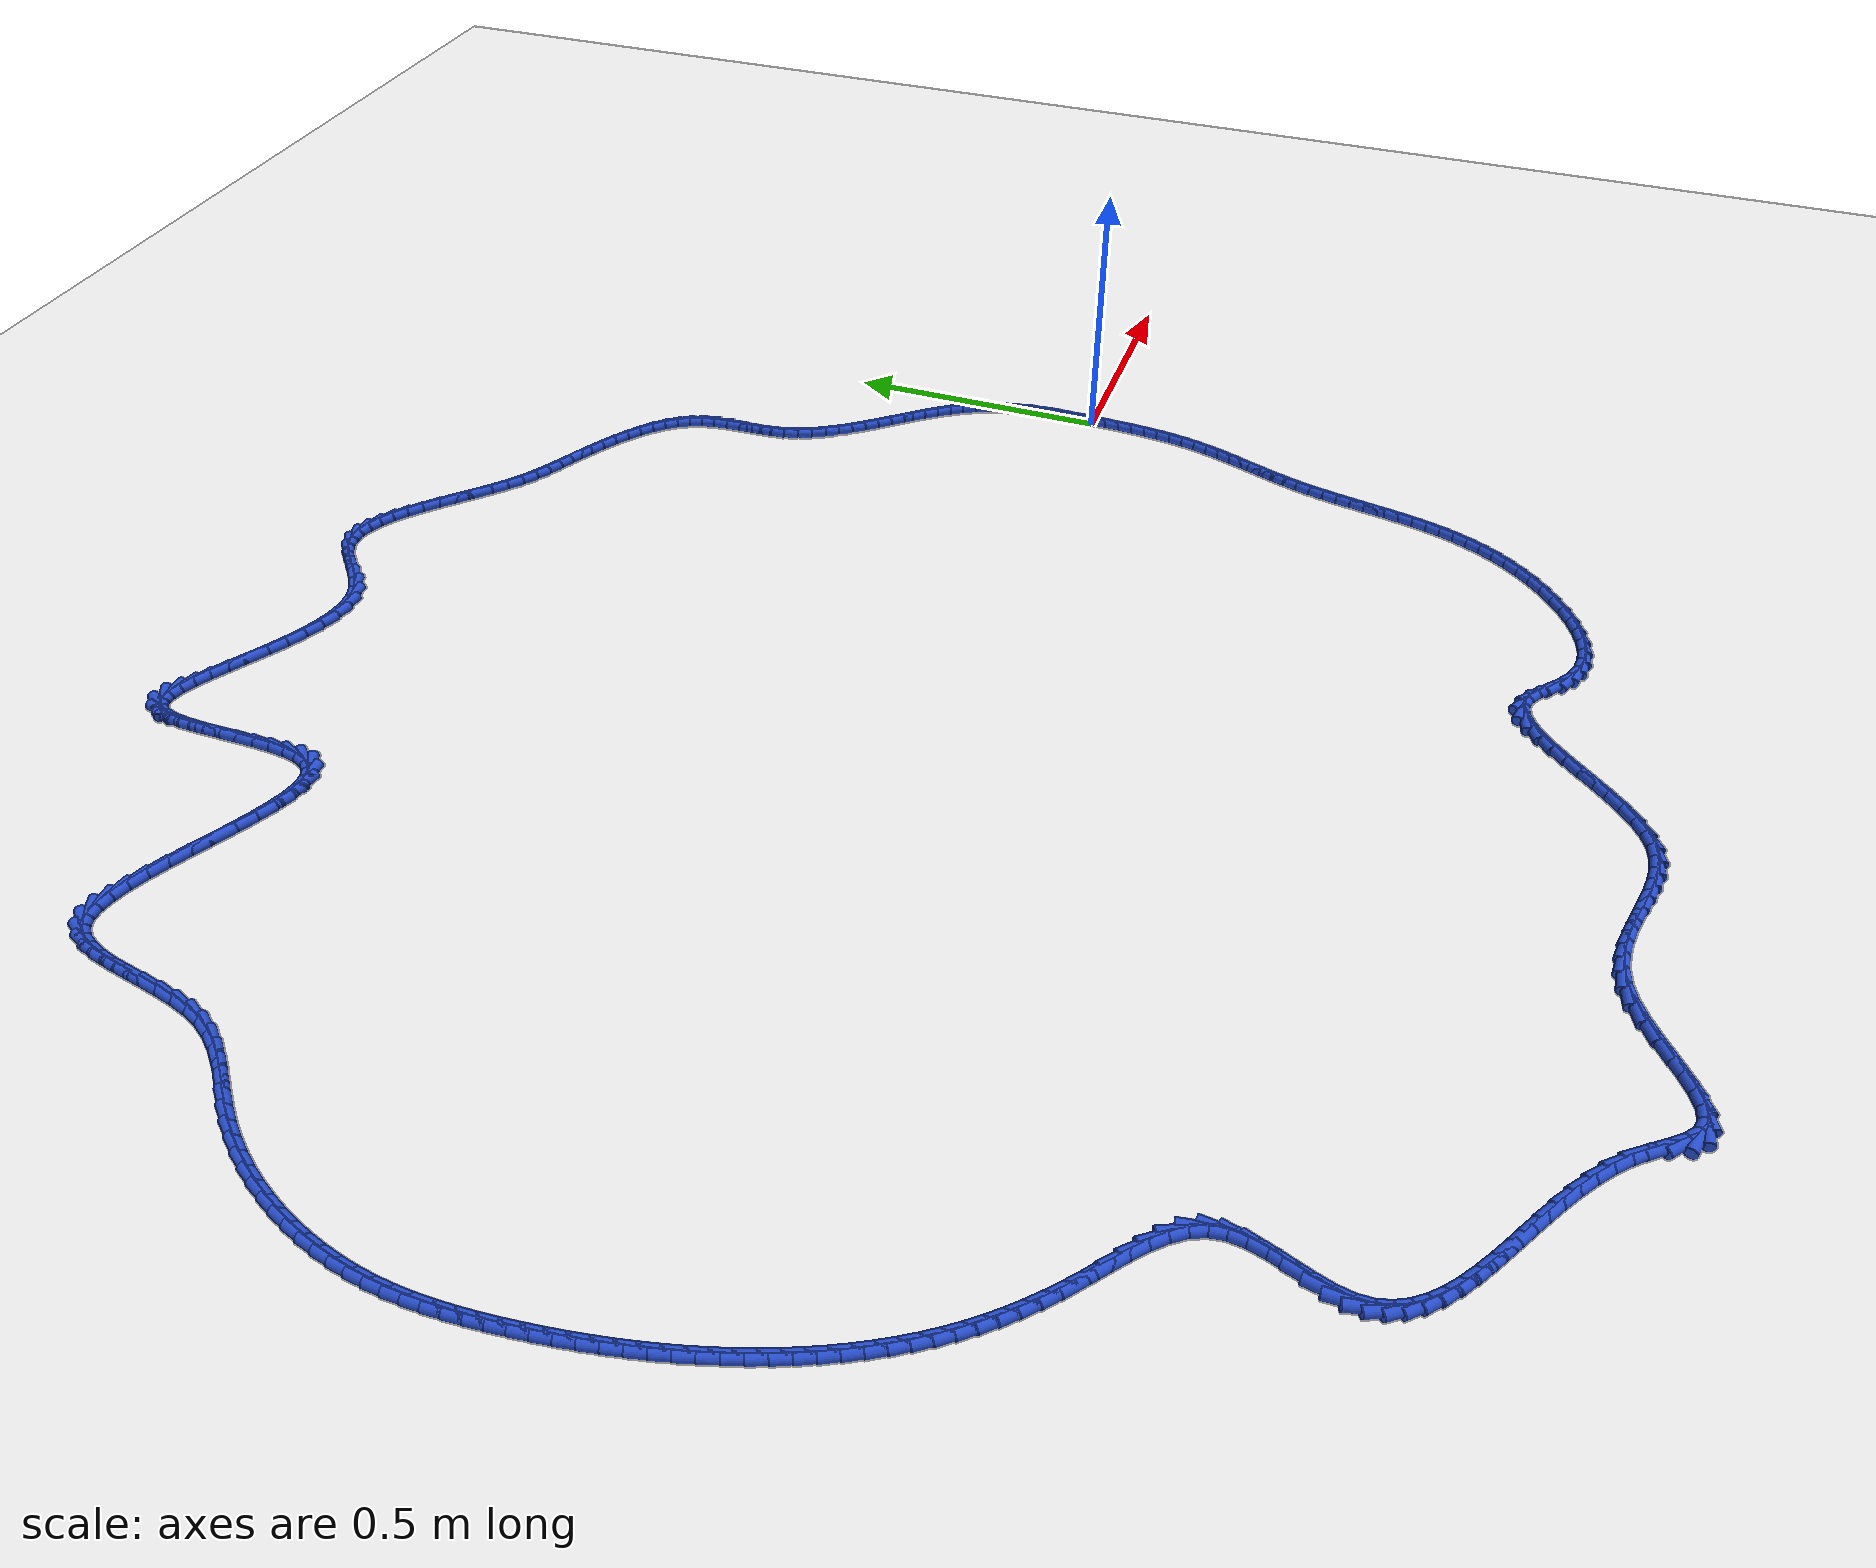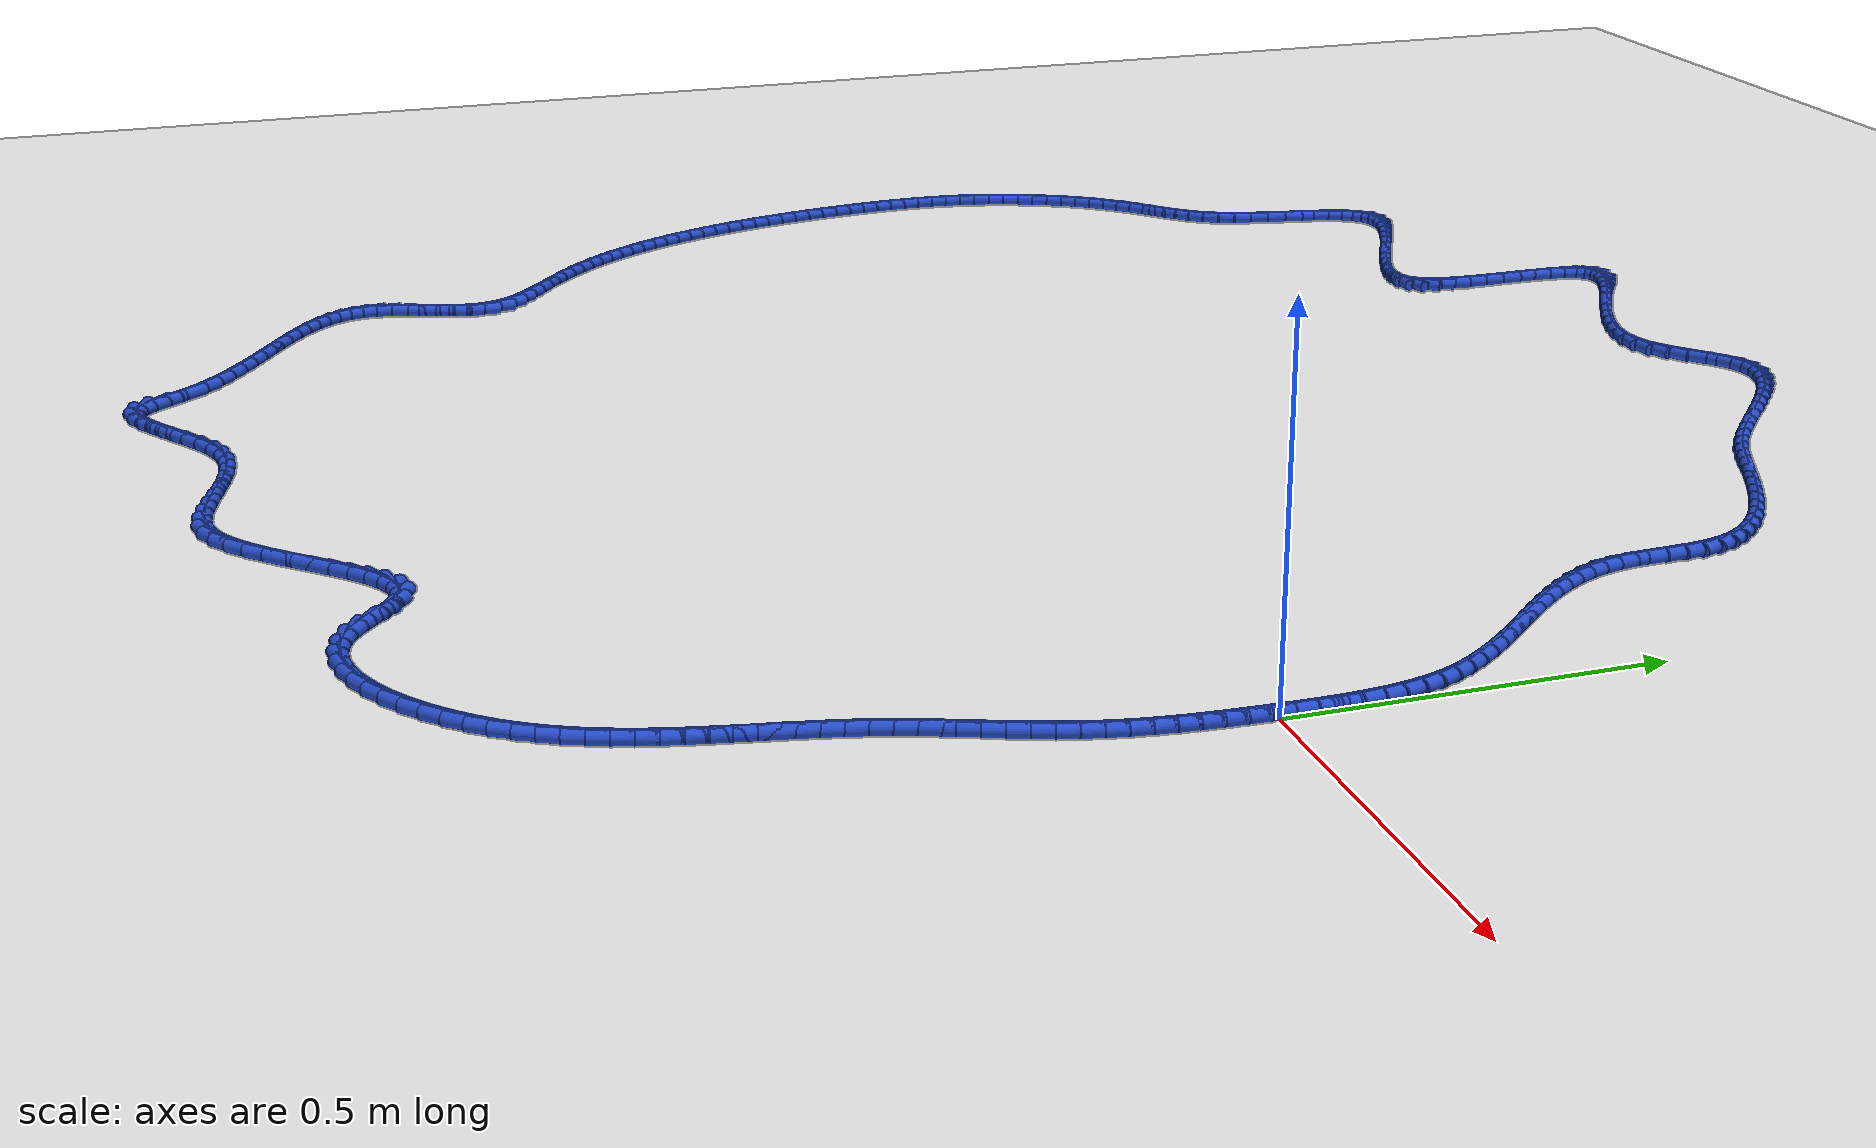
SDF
<sdf version="1.6">
 <world name="default">
  <light name="sun" type="directional">
   <pose>0 0 10 0 -0 0</pose>
   <diffuse>0.8 0.8 0.8 1</diffuse>
   <specular>0.2 0.2 0.2 1</specular>
   <attenuation>
    <range>1000</range>
    <constant>0.9</constant>
    <linear>0.01</linear>
    <quadratic>0.001</quadratic>
   </attenuation>
   <direction>-0.5 0.1 -0.9</direction>
  </light>
  <model name="ground_plane">
   <static>1</static>
   <link name="link">
    <collision name="collision">
     <geometry><plane><normal>0 0 1</normal><size>100 100</size></plane></geometry>
     <surface><friction><ode><mu>100</mu><mu2>50</mu2></ode></friction></surface>
    </collision>
    <visual name="visual">
     <cast_shadows>0</cast_shadows>
     <geometry><plane><normal>0 0 1</normal><size>100 100</size></plane></geometry>
     <material>
      <script><uri>file://media/materials/scripts/gazebo.material</uri><name>Gazebo/WhiteGlow</name></script>
     </material>
    </visual>
   </link>
  </model>
  <gravity>0 0 -9.8</gravity>
  <magnetic_field>6e-06 2.3e-05 -4.2e-05</magnetic_field>
  <atmosphere type="adiabatic"/>
  <physics name="default_physics" default="0" type="ode">
   <max_step_size>0.001</max_step_size>
   <real_time_factor>1</real_time_factor>
   <real_time_update_rate>1000</real_time_update_rate>
  </physics>
  <scene><ambient>0.4 0.4 0.4 1</ambient><background>0.7 0.7 0.7 1</background><shadows>1</shadows></scene>
  <spherical_coordinates>
   <surface_model>EARTH_WGS84</surface_model>
   <latitude_deg>0</latitude_deg>
   <longitude_deg>0</longitude_deg>
   <elevation>0</elevation>
   <heading_deg>0</heading_deg>
  </spherical_coordinates>
  <model name="line">
   <link name="link_0">
    <pose>5.366800753803247e-18 2.7755575615628914e-17 0.01 0 1.57 1.5487285073971115</pose>
    <collision name="collision">
     <geometry><cylinder><radius>0.01</radius><length>0.08</length></cylinder></geometry>
    </collision>
    <visual name="visual">
     <material>
      <script><name>Gazebo/Blue</name><uri>file://media/materials/scripts/gazebo.material</uri></script>
     </material>
     <geometry><cylinder><radius>0.01</radius><length>0.08</length></cylinder></geometry>
    </visual>
   </link>
   <link name="link_1">
    <pose>0.000620939584541092 0.02813321847680312 0.01 0 1.57 1.5651818861590454</pose>
    <collision name="collision">
     <geometry><cylinder><radius>0.01</radius><length>0.08</length></cylinder></geometry>
    </collision>
    <visual name="visual">
     <material>
      <script><name>Gazebo/Blue</name><uri>file://media/materials/scripts/gazebo.material</uri></script>
     </material>
     <geometry><cylinder><radius>0.01</radius><length>0.08</length></cylinder></geometry>
    </visual>
   </link>
   <link name="link_2">
    <pose>0.0007790679116315842 0.05629749624531425 0.01 0 1.57 -1.5500891048895007</pose>
    <collision name="collision">
     <geometry><cylinder><radius>0.01</radius><length>0.08</length></cylinder></geometry>
    </collision>
    <visual name="visual">
     <material>
      <script><name>Gazebo/Blue</name><uri>file://media/materials/scripts/gazebo.material</uri></script>
     </material>
     <geometry><cylinder><radius>0.01</radius><length>0.08</length></cylinder></geometry>
    </visual>
   </link>
   <link name="link_3">
    <pose>0.0001979138139402434 0.08435877041345025 0.01 0 1.57 -1.5134664721738142</pose>
    <collision name="collision">
     <geometry><cylinder><radius>0.01</radius><length>0.08</length></cylinder></geometry>
    </collision>
    <visual name="visual">
     <material>
      <script><name>Gazebo/Blue</name><uri>file://media/materials/scripts/gazebo.material</uri></script>
     </material>
     <geometry><cylinder><radius>0.01</radius><length>0.08</length></cylinder></geometry>
    </visual>
   </link>
   <link name="link_4">
    <pose>-0.001398993875864168 0.11218297808912789 0.01 0 1.57 -1.4659433553836858</pose>
    <collision name="collision">
     <geometry><cylinder><radius>0.01</radius><length>0.08</length></cylinder></geometry>
    </collision>
    <visual name="visual">
     <material>
      <script><name>Gazebo/Blue</name><uri>file://media/materials/scripts/gazebo.material</uri></script>
     </material>
     <geometry><cylinder><radius>0.01</radius><length>0.08</length></cylinder></geometry>
    </visual>
   </link>
   <link name="link_5">
    <pose>-0.004288126325112888 0.13963605638026394 0.01 0 1.57 -1.4068569273346656</pose>
    <collision name="collision">
     <geometry><cylinder><radius>0.01</radius><length>0.08</length></cylinder></geometry>
    </collision>
    <visual name="visual">
     <material>
      <script><name>Gazebo/Blue</name><uri>file://media/materials/scripts/gazebo.material</uri></script>
     </material>
     <geometry><cylinder><radius>0.01</radius><length>0.08</length></cylinder></geometry>
    </visual>
   </link>
   <link name="link_6">
    <pose>-0.008745954701137162 0.1665839423947753 0.01 0 1.57 -1.3356494551655287</pose>
    <collision name="collision">
     <geometry><cylinder><radius>0.01</radius><length>0.08</length></cylinder></geometry>
    </collision>
    <visual name="visual">
     <material>
      <script><name>Gazebo/Blue</name><uri>file://media/materials/scripts/gazebo.material</uri></script>
     </material>
     <geometry><cylinder><radius>0.01</radius><length>0.08</length></cylinder></geometry>
    </visual>
   </link>
   <link name="link_7">
    <pose>-0.015048950171268215 0.19289257324057857 0.01 0 1.57 -1.2521200874395373</pose>
    <collision name="collision">
     <geometry><cylinder><radius>0.01</radius><length>0.08</length></cylinder></geometry>
    </collision>
    <visual name="visual">
     <material>
      <script><name>Gazebo/Blue</name><uri>file://media/materials/scripts/gazebo.material</uri></script>
     </material>
     <geometry><cylinder><radius>0.01</radius><length>0.08</length></cylinder></geometry>
    </visual>
   </link>
   <link name="link_8">
    <pose>-0.023473583902837297 0.2184278860255907 0.01 0 1.57 -1.1592079743053723</pose>
    <collision name="collision">
     <geometry><cylinder><radius>0.01</radius><length>0.08</length></cylinder></geometry>
    </collision>
    <visual name="visual">
     <material>
      <script><name>Gazebo/Blue</name><uri>file://media/materials/scripts/gazebo.material</uri></script>
     </material>
     <geometry><cylinder><radius>0.01</radius><length>0.08</length></cylinder></geometry>
    </visual>
   </link>
   <link name="link_9">
    <pose>-0.034235499437380454 0.2430817234303965 0.01 0 1.57 -1.0742457269397332</pose>
    <collision name="collision">
     <geometry><cylinder><radius>0.01</radius><length>0.08</length></cylinder></geometry>
    </collision>
    <visual name="visual">
     <material>
      <script><name>Gazebo/Blue</name><uri>file://media/materials/scripts/gazebo.material</uri></script>
     </material>
     <geometry><cylinder><radius>0.01</radius><length>0.08</length></cylinder></geometry>
    </visual>
   </link>
   <link name="link_10">
    <pose>-0.047149923148034005 0.2669164597964494 0.01 0 1.57 -1.004362986404253</pose>
    <collision name="collision">
     <geometry><cylinder><radius>0.01</radius><length>0.08</length></cylinder></geometry>
    </collision>
    <visual name="visual">
     <material>
      <script><name>Gazebo/Blue</name><uri>file://media/materials/scripts/gazebo.material</uri></script>
     </material>
     <geometry><cylinder><radius>0.01</radius><length>0.08</length></cylinder></geometry>
    </visual>
   </link>
   <link name="link_11">
    <pose>-0.061870185652145554 0.2900634184371774 0.01 0 1.57 -0.9492944754574141</pose>
    <collision name="collision">
     <geometry><cylinder><radius>0.01</radius><length>0.08</length></cylinder></geometry>
    </collision>
    <visual name="visual">
     <material>
      <script><name>Gazebo/Blue</name><uri>file://media/materials/scripts/gazebo.material</uri></script>
     </material>
     <geometry><cylinder><radius>0.01</radius><length>0.08</length></cylinder></geometry>
    </visual>
   </link>
   <link name="link_12">
    <pose>-0.07804916304784443 0.3126541162389206 0.01 0 1.57 -0.9083384957608868</pose>
    <collision name="collision">
     <geometry><cylinder><radius>0.01</radius><length>0.08</length></cylinder></geometry>
    </collision>
    <visual name="visual">
     <material>
      <script><name>Gazebo/Blue</name><uri>file://media/materials/scripts/gazebo.material</uri></script>
     </material>
     <geometry><cylinder><radius>0.01</radius><length>0.08</length></cylinder></geometry>
    </visual>
   </link>
   <link name="link_13">
    <pose>-0.09533973143325988 0.3348200700880185 0.01 0 1.57 -0.8807233316305242</pose>
    <collision name="collision">
     <geometry><cylinder><radius>0.01</radius><length>0.08</length></cylinder></geometry>
    </collision>
    <visual name="visual">
     <material>
      <script><name>Gazebo/Blue</name><uri>file://media/materials/scripts/gazebo.material</uri></script>
     </material>
     <geometry><cylinder><radius>0.01</radius><length>0.08</length></cylinder></geometry>
    </visual>
   </link>
   <link name="link_14">
    <pose>-0.11339476690652123 0.35669279687081135 0.01 0 1.57 -0.8658207516426746</pose>
    <collision name="collision">
     <geometry><cylinder><radius>0.01</radius><length>0.08</length></cylinder></geometry>
    </collision>
    <visual name="visual">
     <material>
      <script><name>Gazebo/Blue</name><uri>file://media/materials/scripts/gazebo.material</uri></script>
     </material>
     <geometry><cylinder><radius>0.01</radius><length>0.08</length></cylinder></geometry>
    </visual>
   </link>
   <link name="link_15">
    <pose>-0.1318671455657577 0.3784038134736387 0.01 0 1.57 -0.8632602860773909</pose>
    <collision name="collision">
     <geometry><cylinder><radius>0.01</radius><length>0.08</length></cylinder></geometry>
    </collision>
    <visual name="visual">
     <material>
      <script><name>Gazebo/Blue</name><uri>file://media/materials/scripts/gazebo.material</uri></script>
     </material>
     <geometry><cylinder><radius>0.01</radius><length>0.08</length></cylinder></geometry>
    </visual>
   </link>
   <link name="link_16">
    <pose>-0.1504097435090987 0.40008463678284073 0.01 0 1.57 -0.8729798633366467</pose>
    <collision name="collision">
     <geometry><cylinder><radius>0.01</radius><length>0.08</length></cylinder></geometry>
    </collision>
    <visual name="visual">
     <material>
      <script><name>Gazebo/Blue</name><uri>file://media/materials/scripts/gazebo.material</uri></script>
     </material>
     <geometry><cylinder><radius>0.01</radius><length>0.08</length></cylinder></geometry>
    </visual>
   </link>
   <link name="link_17">
    <pose>-0.1686754368346734 0.421866783684757 0.01 0 1.57 -0.8952340096742046</pose>
    <collision name="collision">
     <geometry><cylinder><radius>0.01</radius><length>0.08</length></cylinder></geometry>
    </collision>
    <visual name="visual">
     <material>
      <script><name>Gazebo/Blue</name><uri>file://media/materials/scripts/gazebo.material</uri></script>
     </material>
     <geometry><cylinder><radius>0.01</radius><length>0.08</length></cylinder></geometry>
    </visual>
   </link>
   <link name="link_18">
    <pose>-0.18631710164061102 0.4438817710657274 0.01 0 1.57 -0.9305632364933639</pose>
    <collision name="collision">
     <geometry><cylinder><radius>0.01</radius><length>0.08</length></cylinder></geometry>
    </collision>
    <visual name="visual">
     <material>
      <script><name>Gazebo/Blue</name><uri>file://media/materials/scripts/gazebo.material</uri></script>
     </material>
     <geometry><cylinder><radius>0.01</radius><length>0.08</length></cylinder></geometry>
    </visual>
   </link>
   <link name="link_19">
    <pose>-0.20298761402504106 0.46626111581209206 0.01 0 1.57 -0.9797103766423403</pose>
    <collision name="collision">
     <geometry><cylinder><radius>0.01</radius><length>0.08</length></cylinder></geometry>
    </collision>
    <visual name="visual">
     <material>
      <script><name>Gazebo/Blue</name><uri>file://media/materials/scripts/gazebo.material</uri></script>
     </material>
     <geometry><cylinder><radius>0.01</radius><length>0.08</length></cylinder></geometry>
    </visual>
   </link>
   <link name="link_20">
    <pose>-0.21833985008609264 0.4891363348101906 0.01 0 1.57 -1.043452985396275</pose>
    <collision name="collision">
     <geometry><cylinder><radius>0.01</radius><length>0.08</length></cylinder></geometry>
    </collision>
    <visual name="visual">
     <material>
      <script><name>Gazebo/Blue</name><uri>file://media/materials/scripts/gazebo.material</uri></script>
     </material>
     <geometry><cylinder><radius>0.01</radius><length>0.08</length></cylinder></geometry>
    </visual>
   </link>
   <link name="link_21">
    <pose>-0.23202668592189513 0.512638944946363 0.01 0 1.57 -1.1223125879774722</pose>
    <collision name="collision">
     <geometry><cylinder><radius>0.01</radius><length>0.08</length></cylinder></geometry>
    </collision>
    <visual name="visual">
     <material>
      <script><name>Gazebo/Blue</name><uri>file://media/materials/scripts/gazebo.material</uri></script>
     </material>
     <geometry><cylinder><radius>0.01</radius><length>0.08</length></cylinder></geometry>
    </visual>
   </link>
   <link name="link_22">
    <pose>-0.24370099763057776 0.5369004631069489 0.01 0 1.57 -1.2161211200919668</pose>
    <collision name="collision">
     <geometry><cylinder><radius>0.01</radius><length>0.08</length></cylinder></geometry>
    </collision>
    <visual name="visual">
     <material>
      <script><name>Gazebo/Blue</name><uri>file://media/materials/scripts/gazebo.material</uri></script>
     </material>
     <geometry><cylinder><radius>0.01</radius><length>0.08</length></cylinder></geometry>
    </visual>
   </link>
   <link name="link_23">
    <pose>-0.25301566131026987 0.5620524061782886 0.01 0 1.57 -1.3235025358801134</pose>
    <collision name="collision">
     <geometry><cylinder><radius>0.01</radius><length>0.08</length></cylinder></geometry>
    </collision>
    <visual name="visual">
     <material>
      <script><name>Gazebo/Blue</name><uri>file://media/materials/scripts/gazebo.material</uri></script>
     </material>
     <geometry><cylinder><radius>0.01</radius><length>0.08</length></cylinder></geometry>
    </visual>
   </link>
   <link name="link_24">
    <pose>-0.2596235530591008 0.5882262910467216 0.01 0 1.57 -1.4326529253897289</pose>
    <collision name="collision">
     <geometry><cylinder><radius>0.01</radius><length>0.08</length></cylinder></geometry>
    </collision>
    <visual name="visual">
     <material>
      <script><name>Gazebo/Blue</name><uri>file://media/materials/scripts/gazebo.material</uri></script>
     </material>
     <geometry><cylinder><radius>0.01</radius><length>0.08</length></cylinder></geometry>
    </visual>
   </link>
   <link name="link_25">
    <pose>-0.2634096884339429 0.6154590091943956 0.01 0 1.57 -1.5043987758664819</pose>
    <collision name="collision">
     <geometry><cylinder><radius>0.01</radius><length>0.08</length></cylinder></geometry>
    </collision>
    <visual name="visual">
     <material>
      <script><name>Gazebo/Blue</name><uri>file://media/materials/scripts/gazebo.material</uri></script>
     </material>
     <geometry><cylinder><radius>0.01</radius><length>0.08</length></cylinder></geometry>
    </visual>
   </link>
   <link name="link_26">
    <pose>-0.26526610141909474 0.643376968137311 0.01 0 1.57 -1.5319897572294738</pose>
    <collision name="collision">
     <geometry><cylinder><radius>0.01</radius><length>0.08</length></cylinder></geometry>
    </collision>
    <visual name="visual">
     <material>
      <script><name>Gazebo/Blue</name><uri>file://media/materials/scripts/gazebo.material</uri></script>
     </material>
     <geometry><cylinder><radius>0.01</radius><length>0.08</length></cylinder></geometry>
    </visual>
   </link>
   <link name="link_27">
    <pose>-0.2663578252922254 0.6714952945751038 0.01 0 1.57 -1.517241108202471</pose>
    <collision name="collision">
     <geometry><cylinder><radius>0.01</radius><length>0.08</length></cylinder></geometry>
    </collision>
    <visual name="visual">
     <material>
      <script><name>Gazebo/Blue</name><uri>file://media/materials/scripts/gazebo.material</uri></script>
     </material>
     <geometry><cylinder><radius>0.01</radius><length>0.08</length></cylinder></geometry>
    </visual>
   </link>
   <link name="link_28">
    <pose>-0.2678498983067601 0.6993291131791767 0.01 0 1.57 -1.458303586060912</pose>
    <collision name="collision">
     <geometry><cylinder><radius>0.01</radius><length>0.08</length></cylinder></geometry>
    </collision>
    <visual name="visual">
     <material>
      <script><name>Gazebo/Blue</name><uri>file://media/materials/scripts/gazebo.material</uri></script>
     </material>
     <geometry><cylinder><radius>0.01</radius><length>0.08</length></cylinder></geometry>
    </visual>
   </link>
   <link name="link_29">
    <pose>-0.27090735871612426 0.7263935486209322 0.01 0 1.57 -1.3501975612696395</pose>
    <collision name="collision">
     <geometry><cylinder><radius>0.01</radius><length>0.08</length></cylinder></geometry>
    </collision>
    <visual name="visual">
     <material>
      <script><name>Gazebo/Blue</name><uri>file://media/materials/scripts/gazebo.material</uri></script>
     </material>
     <geometry><cylinder><radius>0.01</radius><length>0.08</length></cylinder></geometry>
    </visual>
   </link>
   <link name="link_30">
    <pose>-0.2766952447737433 0.7522037255717733 0.01 0 1.57 -1.1950326874212696</pose>
    <collision name="collision">
     <geometry><cylinder><radius>0.01</radius><length>0.08</length></cylinder></geometry>
    </collision>
    <visual name="visual">
     <material>
      <script><name>Gazebo/Blue</name><uri>file://media/materials/scripts/gazebo.material</uri></script>
     </material>
     <geometry><cylinder><radius>0.01</radius><length>0.08</length></cylinder></geometry>
    </visual>
   </link>
   <link name="link_31">
    <pose>-0.28621562427091757 0.7763359616284502 0.01 0 1.57 -1.0385113715244263</pose>
    <collision name="collision">
     <geometry><cylinder><radius>0.01</radius><length>0.08</length></cylinder></geometry>
    </collision>
    <visual name="visual">
     <material>
      <script><name>Gazebo/Blue</name><uri>file://media/materials/scripts/gazebo.material</uri></script>
     </material>
     <geometry><cylinder><radius>0.01</radius><length>0.08</length></cylinder></geometry>
    </visual>
   </link>
   <link name="link_32">
    <pose>-0.2994231002447276 0.798759881442713 0.01 0 1.57 -0.9030539173214832</pose>
    <collision name="collision">
     <geometry><cylinder><radius>0.01</radius><length>0.08</length></cylinder></geometry>
    </collision>
    <visual name="visual">
     <material>
      <script><name>Gazebo/Blue</name><uri>file://media/materials/scripts/gazebo.material</uri></script>
     </material>
     <geometry><cylinder><radius>0.01</radius><length>0.08</length></cylinder></geometry>
    </visual>
   </link>
   <link name="link_33">
    <pose>-0.3158578858903623 0.8196007067378854 0.01 0 1.57 -0.7901164934247928</pose>
    <collision name="collision">
     <geometry><cylinder><radius>0.01</radius><length>0.08</length></cylinder></geometry>
    </collision>
    <visual name="visual">
     <material>
      <script><name>Gazebo/Blue</name><uri>file://media/materials/scripts/gazebo.material</uri></script>
     </material>
     <geometry><cylinder><radius>0.01</radius><length>0.08</length></cylinder></geometry>
    </visual>
   </link>
   <link name="link_34">
    <pose>-0.335059167612795 0.8389840447813733 0.01 0 1.57 -0.6982673568344422</pose>
    <collision name="collision">
     <geometry><cylinder><radius>0.01</radius><length>0.08</length></cylinder></geometry>
    </collision>
    <visual name="visual">
     <material>
      <script><name>Gazebo/Blue</name><uri>file://media/materials/scripts/gazebo.material</uri></script>
     </material>
     <geometry><cylinder><radius>0.01</radius><length>0.08</length></cylinder></geometry>
    </visual>
   </link>
   <link name="link_35">
    <pose>-0.3565661318169987 0.8570355028405823 0.01 0 1.57 -0.6249211696366177</pose>
    <collision name="collision">
     <geometry><cylinder><radius>0.01</radius><length>0.08</length></cylinder></geometry>
    </collision>
    <visual name="visual">
     <material>
      <script><name>Gazebo/Blue</name><uri>file://media/materials/scripts/gazebo.material</uri></script>
     </material>
     <geometry><cylinder><radius>0.01</radius><length>0.08</length></cylinder></geometry>
    </visual>
   </link>
   <link name="link_36">
    <pose>-0.3799179649079465 0.8738806881829176 0.01 0 1.57 -0.5674051294833872</pose>
    <collision name="collision">
     <geometry><cylinder><radius>0.01</radius><length>0.08</length></cylinder></geometry>
    </collision>
    <visual name="visual">
     <material>
      <script><name>Gazebo/Blue</name><uri>file://media/materials/scripts/gazebo.material</uri></script>
     </material>
     <geometry><cylinder><radius>0.01</radius><length>0.08</length></cylinder></geometry>
    </visual>
   </link>
   <link name="link_37">
    <pose>-0.40465385329061176 0.8896452080757851 0.01 0 1.57 -0.5234571785244676</pose>
    <collision name="collision">
     <geometry><cylinder><radius>0.01</radius><length>0.08</length></cylinder></geometry>
    </collision>
    <visual name="visual">
     <material>
      <script><name>Gazebo/Blue</name><uri>file://media/materials/scripts/gazebo.material</uri></script>
     </material>
     <geometry><cylinder><radius>0.01</radius><length>0.08</length></cylinder></geometry>
    </visual>
   </link>
   <link name="link_38">
    <pose>-0.4303129833699673 0.90445466978659 0.01 0 1.57 -0.49140213225383594</pose>
    <collision name="collision">
     <geometry><cylinder><radius>0.01</radius><length>0.08</length></cylinder></geometry>
    </collision>
    <visual name="visual">
     <material>
      <script><name>Gazebo/Blue</name><uri>file://media/materials/scripts/gazebo.material</uri></script>
     </material>
     <geometry><cylinder><radius>0.01</radius><length>0.08</length></cylinder></geometry>
    </visual>
   </link>
   <link name="link_39">
    <pose>-0.4564345415509868 0.9184346805827381 0.01 0 1.57 -0.47019734979528466</pose>
    <collision name="collision">
     <geometry><cylinder><radius>0.01</radius><length>0.08</length></cylinder></geometry>
    </collision>
    <visual name="visual">
     <material>
      <script><name>Gazebo/Blue</name><uri>file://media/materials/scripts/gazebo.material</uri></script>
     </material>
     <geometry><cylinder><radius>0.01</radius><length>0.08</length></cylinder></geometry>
    </visual>
   </link>
   <link name="link_40">
    <pose>-0.4825577142386427 0.9317108477316346 0.01 0 1.57 -0.45946007573270226</pose>
    <collision name="collision">
     <geometry><cylinder><radius>0.01</radius><length>0.08</length></cylinder></geometry>
    </collision>
    <visual name="visual">
     <material>
      <script><name>Gazebo/Blue</name><uri>file://media/materials/scripts/gazebo.material</uri></script>
     </material>
     <geometry><cylinder><radius>0.01</radius><length>0.08</length></cylinder></geometry>
    </visual>
   </link>
   <link name="link_41">
    <pose>-0.5082216878379086 0.9444087785006853 0.01 0 1.57 -0.46028715344471816</pose>
    <collision name="collision">
     <geometry><cylinder><radius>0.01</radius><length>0.08</length></cylinder></geometry>
    </collision>
    <visual name="visual">
     <material>
      <script><name>Gazebo/Blue</name><uri>file://media/materials/scripts/gazebo.material</uri></script>
     </material>
     <geometry><cylinder><radius>0.01</radius><length>0.08</length></cylinder></geometry>
    </visual>
   </link>
   <link name="link_42">
    <pose>-0.5330084450096235 0.9566982128504474 0.01 0 1.57 -0.4823046942819314</pose>
    <collision name="collision">
     <geometry><cylinder><radius>0.01</radius><length>0.08</length></cylinder></geometry>
    </collision>
    <visual name="visual">
     <material>
      <script><name>Gazebo/Blue</name><uri>file://media/materials/scripts/gazebo.material</uri></script>
     </material>
     <geometry><cylinder><radius>0.01</radius><length>0.08</length></cylinder></geometry>
    </visual>
   </link>
   <link name="link_43">
    <pose>-0.5569887793671398 0.9692529662345301 0.01 0 1.57 -0.5304118967696</pose>
    <collision name="collision">
     <geometry><cylinder><radius>0.01</radius><length>0.08</length></cylinder></geometry>
    </collision>
    <visual name="visual">
     <material>
      <script><name>Gazebo/Blue</name><uri>file://media/materials/scripts/gazebo.material</uri></script>
     </material>
     <geometry><cylinder><radius>0.01</radius><length>0.08</length></cylinder></geometry>
    </visual>
   </link>
   <link name="link_44">
    <pose>-0.5805447659667639 0.9830678562159035 0.01 0 1.57 -0.5993380845933235</pose>
    <collision name="collision">
     <geometry><cylinder><radius>0.01</radius><length>0.08</length></cylinder></geometry>
    </collision>
    <visual name="visual">
     <material>
      <script><name>Gazebo/Blue</name><uri>file://media/materials/scripts/gazebo.material</uri></script>
     </material>
     <geometry><cylinder><radius>0.01</radius><length>0.08</length></cylinder></geometry>
    </visual>
   </link>
   <link name="link_45">
    <pose>-0.6040610722466377 0.9991333860037775 0.01 0 1.57 -0.667412638063135</pose>
    <collision name="collision">
     <geometry><cylinder><radius>0.01</radius><length>0.08</length></cylinder></geometry>
    </collision>
    <visual name="visual">
     <material>
      <script><name>Gazebo/Blue</name><uri>file://media/materials/scripts/gazebo.material</uri></script>
     </material>
     <geometry><cylinder><radius>0.01</radius><length>0.08</length></cylinder></geometry>
    </visual>
   </link>
   <link name="link_46">
    <pose>-0.6277620611789947 1.0178109839294376 0.01 0 1.57 -0.7133157236568874</pose>
    <collision name="collision">
     <geometry><cylinder><radius>0.01</radius><length>0.08</length></cylinder></geometry>
    </collision>
    <visual name="visual">
     <material>
      <script><name>Gazebo/Blue</name><uri>file://media/materials/scripts/gazebo.material</uri></script>
     </material>
     <geometry><cylinder><radius>0.01</radius><length>0.08</length></cylinder></geometry>
    </visual>
   </link>
   <link name="link_47">
    <pose>-0.6516143502089071 1.038450620314482 0.01 0 1.57 -0.739876196833175</pose>
    <collision name="collision">
     <geometry><cylinder><radius>0.01</radius><length>0.08</length></cylinder></geometry>
    </collision>
    <visual name="visual">
     <material>
      <script><name>Gazebo/Blue</name><uri>file://media/materials/scripts/gazebo.material</uri></script>
     </material>
     <geometry><cylinder><radius>0.01</radius><length>0.08</length></cylinder></geometry>
    </visual>
   </link>
   <link name="link_48">
    <pose>-0.6755612646709673 1.0603108614046814 0.01 0 1.57 -0.7498927699195483</pose>
    <collision name="collision">
     <geometry><cylinder><radius>0.01</radius><length>0.08</length></cylinder></geometry>
    </collision>
    <visual name="visual">
     <material>
      <script><name>Gazebo/Blue</name><uri>file://media/materials/scripts/gazebo.material</uri></script>
     </material>
     <geometry><cylinder><radius>0.01</radius><length>0.08</length></cylinder></geometry>
    </visual>
   </link>
   <link name="link_49">
    <pose>-0.6995461298997675 1.0826502734458059 0.01 0 1.57 -0.7443947227776282</pose>
    <collision name="collision">
     <geometry><cylinder><radius>0.01</radius><length>0.08</length></cylinder></geometry>
    </collision>
    <visual name="visual">
     <material>
      <script><name>Gazebo/Blue</name><uri>file://media/materials/scripts/gazebo.material</uri></script>
     </material>
     <geometry><cylinder><radius>0.01</radius><length>0.08</length></cylinder></geometry>
    </visual>
   </link>
   <link name="link_50">
    <pose>-0.7235122712298993 1.1047274226836252 0.01 0 1.57 -0.7228236638282604</pose>
    <collision name="collision">
     <geometry><cylinder><radius>0.01</radius><length>0.08</length></cylinder></geometry>
    </collision>
    <visual name="visual">
     <material>
      <script><name>Gazebo/Blue</name><uri>file://media/materials/scripts/gazebo.material</uri></script>
     </material>
     <geometry><cylinder><radius>0.01</radius><length>0.08</length></cylinder></geometry>
    </visual>
   </link>
   <link name="link_51">
    <pose>-0.7474030139959547 1.1258008753639097 0.01 0 1.57 -0.6829349419545444</pose>
    <collision name="collision">
     <geometry><cylinder><radius>0.01</radius><length>0.08</length></cylinder></geometry>
    </collision>
    <visual name="visual">
     <material>
      <script><name>Gazebo/Blue</name><uri>file://media/materials/scripts/gazebo.material</uri></script>
     </material>
     <geometry><cylinder><radius>0.01</radius><length>0.08</length></cylinder></geometry>
    </visual>
   </link>
   <link name="link_52">
    <pose>-0.7711616835325255 1.1451291977324305 0.01 0 1.57 -0.6204208351398596</pose>
    <collision name="collision">
     <geometry><cylinder><radius>0.01</radius><length>0.08</length></cylinder></geometry>
    </collision>
    <visual name="visual">
     <material>
      <script><name>Gazebo/Blue</name><uri>file://media/materials/scripts/gazebo.material</uri></script>
     </material>
     <geometry><cylinder><radius>0.01</radius><length>0.08</length></cylinder></geometry>
    </visual>
   </link>
   <link name="link_53">
    <pose>-0.794731605174204 1.161970956034957 0.01 0 1.57 -0.5283240076845835</pose>
    <collision name="collision">
     <geometry><cylinder><radius>0.01</radius><length>0.08</length></cylinder></geometry>
    </collision>
    <visual name="visual">
     <material>
      <script><name>Gazebo/Blue</name><uri>file://media/materials/scripts/gazebo.material</uri></script>
     </material>
     <geometry><cylinder><radius>0.01</radius><length>0.08</length></cylinder></geometry>
    </visual>
   </link>
   <link name="link_54">
    <pose>-0.8180561042555821 1.1755847165172597 0.01 0 1.57 -0.39670161299615847</pose>
    <collision name="collision">
     <geometry><cylinder><radius>0.01</radius><length>0.08</length></cylinder></geometry>
    </collision>
    <visual name="visual">
     <material>
      <script><name>Gazebo/Blue</name><uri>file://media/materials/scripts/gazebo.material</uri></script>
     </material>
     <geometry><cylinder><radius>0.01</radius><length>0.08</length></cylinder></geometry>
    </visual>
   </link>
   <link name="link_55">
    <pose>-0.8410785061112516 1.1852290454251082 0.01 0 1.57 -0.21433821414498522</pose>
    <collision name="collision">
     <geometry><cylinder><radius>0.01</radius><length>0.08</length></cylinder></geometry>
    </collision>
    <visual name="visual">
     <material>
      <script><name>Gazebo/Blue</name><uri>file://media/materials/scripts/gazebo.material</uri></script>
     </material>
     <geometry><cylinder><radius>0.01</radius><length>0.08</length></cylinder></geometry>
    </visual>
   </link>
   <link name="link_56">
    <pose>-0.8637421360758044 1.1901625090042742 0.01 0 1.57 0.023316127460977106</pose>
    <collision name="collision">
     <geometry><cylinder><radius>0.01</radius><length>0.08</length></cylinder></geometry>
    </collision>
    <visual name="visual">
     <material>
      <script><name>Gazebo/Blue</name><uri>file://media/materials/scripts/gazebo.material</uri></script>
     </material>
     <geometry><cylinder><radius>0.01</radius><length>0.08</length></cylinder></geometry>
    </visual>
   </link>
   <link name="link_57">
    <pose>-0.8859903194838331 1.1896436735005274 0.01 0 1.57 0.29900089032532334</pose>
    <collision name="collision">
     <geometry><cylinder><radius>0.01</radius><length>0.08</length></cylinder></geometry>
    </collision>
    <visual name="visual">
     <material>
      <script><name>Gazebo/Blue</name><uri>file://media/materials/scripts/gazebo.material</uri></script>
     </material>
     <geometry><cylinder><radius>0.01</radius><length>0.08</length></cylinder></geometry>
    </visual>
   </link>
   <link name="link_58">
    <pose>-0.9077664234146512 1.1829313664147667 0.01 0 1.57 0.54584681754813</pose>
    <collision name="collision">
     <geometry><cylinder><radius>0.01</radius><length>0.08</length></cylinder></geometry>
    </collision>
    <visual name="visual">
     <material>
      <script><name>Gazebo/Blue</name><uri>file://media/materials/scripts/gazebo.material</uri></script>
     </material>
     <geometry><cylinder><radius>0.01</radius><length>0.08</length></cylinder></geometry>
    </visual>
   </link>
   <link name="link_59">
    <pose>-0.9291217661906565 1.1699600171989704 0.01 0 1.57 0.6774727995125979</pose>
    <collision name="collision">
     <geometry><cylinder><radius>0.01</radius><length>0.08</length></cylinder></geometry>
    </collision>
    <visual name="visual">
     <material>
      <script><name>Gazebo/Blue</name><uri>file://media/materials/scripts/gazebo.material</uri></script>
     </material>
     <geometry><cylinder><radius>0.01</radius><length>0.08</length></cylinder></geometry>
    </visual>
   </link>
   <link name="link_60">
    <pose>-0.9504493129809032 1.1528022175864423 0.01 0 1.57 0.71385148640333</pose>
    <collision name="collision">
     <geometry><cylinder><radius>0.01</radius><length>0.08</length></cylinder></geometry>
    </collision>
    <visual name="visual">
     <material>
      <script><name>Gazebo/Blue</name><uri>file://media/materials/scripts/gazebo.material</uri></script>
     </material>
     <geometry><cylinder><radius>0.01</radius><length>0.08</length></cylinder></geometry>
    </visual>
   </link>
   <link name="link_61">
    <pose>-0.9722094553628684 1.1339525406771058 0.01 0 1.57 0.6727047875825343</pose>
    <collision name="collision">
     <geometry><cylinder><radius>0.01</radius><length>0.08</length></cylinder></geometry>
    </collision>
    <visual name="visual">
     <material>
      <script><name>Gazebo/Blue</name><uri>file://media/materials/scripts/gazebo.material</uri></script>
     </material>
     <geometry><cylinder><radius>0.01</radius><length>0.08</length></cylinder></geometry>
    </visual>
   </link>
   <link name="link_62">
    <pose>-0.9948625849140289 1.1159055595708856 0.01 0 1.57 0.5509439379543355</pose>
    <collision name="collision">
     <geometry><cylinder><radius>0.01</radius><length>0.08</length></cylinder></geometry>
    </collision>
    <visual name="visual">
     <material>
      <script><name>Gazebo/Blue</name><uri>file://media/materials/scripts/gazebo.material</uri></script>
     </material>
     <geometry><cylinder><radius>0.01</radius><length>0.08</length></cylinder></geometry>
    </visual>
   </link>
   <link name="link_63">
    <pose>-1.0188690932118623 1.1011558473677054 0.01 0 1.57 0.3350697430768753</pose>
    <collision name="collision">
     <geometry><cylinder><radius>0.01</radius><length>0.08</length></cylinder></geometry>
    </collision>
    <visual name="visual">
     <material>
      <script><name>Gazebo/Blue</name><uri>file://media/materials/scripts/gazebo.material</uri></script>
     </material>
     <geometry><cylinder><radius>0.01</radius><length>0.08</length></cylinder></geometry>
    </visual>
   </link>
   <link name="link_64">
    <pose>-1.0446817697886193 1.0921678911458852 0.01 0 1.57 0.07789485446807431</pose>
    <collision name="collision">
     <geometry><cylinder><radius>0.01</radius><length>0.08</length></cylinder></geometry>
    </collision>
    <visual name="visual">
     <material>
      <script><name>Gazebo/Blue</name><uri>file://media/materials/scripts/gazebo.material</uri></script>
     </material>
     <geometry><cylinder><radius>0.01</radius><length>0.08</length></cylinder></geometry>
    </visual>
   </link>
   <link name="link_65">
    <pose>-1.0723992239979772 1.0900044667089737 0.01 0 1.57 -0.12782673160292443</pose>
    <collision name="collision">
     <geometry><cylinder><radius>0.01</radius><length>0.08</length></cylinder></geometry>
    </collision>
    <visual name="visual">
     <material>
      <script><name>Gazebo/Blue</name><uri>file://media/materials/scripts/gazebo.material</uri></script>
     </material>
     <geometry><cylinder><radius>0.01</radius><length>0.08</length></cylinder></geometry>
    </visual>
   </link>
   <link name="link_66">
    <pose>-1.1016228361733886 1.0937605053396853 0.01 0 1.57 -0.27731115150554414</pose>
    <collision name="collision">
     <geometry><cylinder><radius>0.01</radius><length>0.08</length></cylinder></geometry>
    </collision>
    <visual name="visual">
     <material>
      <script><name>Gazebo/Blue</name><uri>file://media/materials/scripts/gazebo.material</uri></script>
     </material>
     <geometry><cylinder><radius>0.01</radius><length>0.08</length></cylinder></geometry>
    </visual>
   </link>
   <link name="link_67">
    <pose>-1.1319167386660762 1.1023835248859608 0.01 0 1.57 -0.3823498876096761</pose>
    <collision name="collision">
     <geometry><cylinder><radius>0.01</radius><length>0.08</length></cylinder></geometry>
    </collision>
    <visual name="visual">
     <material>
      <script><name>Gazebo/Blue</name><uri>file://media/materials/scripts/gazebo.material</uri></script>
     </material>
     <geometry><cylinder><radius>0.01</radius><length>0.08</length></cylinder></geometry>
    </visual>
   </link>
   <link name="link_68">
    <pose>-1.1628450638272643 1.1148210431957417 0.01 0 1.57 -0.4542511215402282</pose>
    <collision name="collision">
     <geometry><cylinder><radius>0.01</radius><length>0.08</length></cylinder></geometry>
    </collision>
    <visual name="visual">
     <material>
      <script><name>Gazebo/Blue</name><uri>file://media/materials/scripts/gazebo.material</uri></script>
     </material>
     <geometry><cylinder><radius>0.01</radius><length>0.08</length></cylinder></geometry>
    </visual>
   </link>
   <link name="link_69">
    <pose>-1.1939719440081755 1.130020578116969 0.01 0 1.57 -0.5008478500670691</pose>
    <collision name="collision">
     <geometry><cylinder><radius>0.01</radius><length>0.08</length></cylinder></geometry>
    </collision>
    <visual name="visual">
     <material>
      <script><name>Gazebo/Blue</name><uri>file://media/materials/scripts/gazebo.material</uri></script>
     </material>
     <geometry><cylinder><radius>0.01</radius><length>0.08</length></cylinder></geometry>
    </visual>
   </link>
   <link name="link_70">
    <pose>-1.2248615115600339 1.146929647497584 0.01 0 1.57 -0.5265890483183472</pose>
    <collision name="collision">
     <geometry><cylinder><radius>0.01</radius><length>0.08</length></cylinder></geometry>
    </collision>
    <visual name="visual">
     <material>
      <script><name>Gazebo/Blue</name><uri>file://media/materials/scripts/gazebo.material</uri></script>
     </material>
     <geometry><cylinder><radius>0.01</radius><length>0.08</length></cylinder></geometry>
    </visual>
   </link>
   <link name="link_71">
    <pose>-1.2550778988340623 1.1644957691855278 0.01 0 1.57 -0.5329668700387141</pose>
    <collision name="collision">
     <geometry><cylinder><radius>0.01</radius><length>0.08</length></cylinder></geometry>
    </collision>
    <visual name="visual">
     <material>
      <script><name>Gazebo/Blue</name><uri>file://media/materials/scripts/gazebo.material</uri></script>
     </material>
     <geometry><cylinder><radius>0.01</radius><length>0.08</length></cylinder></geometry>
    </visual>
   </link>
   <link name="link_72">
    <pose>-1.284185238181484 1.181666461028741 0.01 0 1.57 -0.5184025050078016</pose>
    <collision name="collision">
     <geometry><cylinder><radius>0.01</radius><length>0.08</length></cylinder></geometry>
    </collision>
    <visual name="visual">
     <material>
      <script><name>Gazebo/Blue</name><uri>file://media/materials/scripts/gazebo.material</uri></script>
     </material>
     <geometry><cylinder><radius>0.01</radius><length>0.08</length></cylinder></geometry>
    </visual>
   </link>
   <link name="link_73">
    <pose>-1.311747661953524 1.1973892408751665 0.01 0 1.57 -0.47705244257798435</pose>
    <collision name="collision">
     <geometry><cylinder><radius>0.01</radius><length>0.08</length></cylinder></geometry>
    </collision>
    <visual name="visual">
     <material>
      <script><name>Gazebo/Blue</name><uri>file://media/materials/scripts/gazebo.material</uri></script>
     </material>
     <geometry><cylinder><radius>0.01</radius><length>0.08</length></cylinder></geometry>
    </visual>
   </link>
   <link name="link_74">
    <pose>-1.3373293025014035 1.2106116265727436 0.01 0 1.57 -0.39543208439316047</pose>
    <collision name="collision">
     <geometry><cylinder><radius>0.01</radius><length>0.08</length></cylinder></geometry>
    </collision>
    <visual name="visual">
     <material>
      <script><name>Gazebo/Blue</name><uri>file://media/materials/scripts/gazebo.material</uri></script>
     </material>
     <geometry><cylinder><radius>0.01</radius><length>0.08</length></cylinder></geometry>
    </visual>
   </link>
   <link name="link_75">
    <pose>-1.3604942921763472 1.2202811359694141 0.01 0 1.57 -0.24433140604695042</pose>
    <collision name="collision">
     <geometry><cylinder><radius>0.01</radius><length>0.08</length></cylinder></geometry>
    </collision>
    <visual name="visual">
     <material>
      <script><name>Gazebo/Blue</name><uri>file://media/materials/scripts/gazebo.material</uri></script>
     </material>
     <geometry><cylinder><radius>0.01</radius><length>0.08</length></cylinder></geometry>
    </visual>
   </link>
   <link name="link_76">
    <pose>-1.3808067633295782 1.225345286913119 0.01 0 1.57 0.03485938675276248</pose>
    <collision name="collision">
     <geometry><cylinder><radius>0.01</radius><length>0.08</length></cylinder></geometry>
    </collision>
    <visual name="visual">
     <material>
      <script><name>Gazebo/Blue</name><uri>file://media/materials/scripts/gazebo.material</uri></script>
     </material>
     <geometry><cylinder><radius>0.01</radius><length>0.08</length></cylinder></geometry>
    </visual>
   </link>
   <link name="link_77">
    <pose>-1.3978308483123199 1.2247515972518 0.01 0 1.57 0.5022140779273673</pose>
    <collision name="collision">
     <geometry><cylinder><radius>0.01</radius><length>0.08</length></cylinder></geometry>
    </collision>
    <visual name="visual">
     <material>
      <script><name>Gazebo/Blue</name><uri>file://media/materials/scripts/gazebo.material</uri></script>
     </material>
     <geometry><cylinder><radius>0.01</radius><length>0.08</length></cylinder></geometry>
    </visual>
   </link>
   <link name="link_78">
    <pose>-1.4111306794757963 1.2174475848333979 0.01 0 1.57 1.0084803409328873</pose>
    <collision name="collision">
     <geometry><cylinder><radius>0.01</radius><length>0.08</length></cylinder></geometry>
    </collision>
    <visual name="visual">
     <material>
      <script><name>Gazebo/Blue</name><uri>file://media/materials/scripts/gazebo.material</uri></script>
     </material>
     <geometry><cylinder><radius>0.01</radius><length>0.08</length></cylinder></geometry>
    </visual>
   </link>
   <link name="link_79">
    <pose>-1.4204280710886583 1.2026940486102145 0.01 0 1.57 1.3050376127300412</pose>
    <collision name="collision">
     <geometry><cylinder><radius>0.01</radius><length>0.08</length></cylinder></geometry>
    </collision>
    <visual name="visual">
     <material>
      <script><name>Gazebo/Blue</name><uri>file://media/materials/scripts/gazebo.material</uri></script>
     </material>
     <geometry><cylinder><radius>0.01</radius><length>0.08</length></cylinder></geometry>
    </visual>
   </link>
   <link name="link_80">
    <pose>-1.4262418623791329 1.181335310005672 0.01 0 1.57 1.4548565718521387</pose>
    <collision name="collision">
     <geometry><cylinder><radius>0.01</radius><length>0.08</length></cylinder></geometry>
    </collision>
    <visual name="visual">
     <material>
      <script><name>Gazebo/Blue</name><uri>file://media/materials/scripts/gazebo.material</uri></script>
     </material>
     <geometry><cylinder><radius>0.01</radius><length>0.08</length></cylinder></geometry>
    </visual>
   </link>
   <link name="link_81">
    <pose>-1.4293421349865743 1.1547148567477672 0.01 0 1.57 1.5329301169874554</pose>
    <collision name="collision">
     <geometry><cylinder><radius>0.01</radius><length>0.08</length></cylinder></geometry>
    </collision>
    <visual name="visual">
     <material>
      <script><name>Gazebo/Blue</name><uri>file://media/materials/scripts/gazebo.material</uri></script>
     </material>
     <geometry><cylinder><radius>0.01</radius><length>0.08</length></cylinder></geometry>
    </visual>
   </link>
   <link name="link_82">
    <pose>-1.430499064962297 1.1241763641413793 0.01 0 1.57 -1.5703059854283532</pose>
    <collision name="collision">
     <geometry><cylinder><radius>0.01</radius><length>0.08</length></cylinder></geometry>
    </collision>
    <visual name="visual">
     <material>
      <script><name>Gazebo/Blue</name><uri>file://media/materials/scripts/gazebo.material</uri></script>
     </material>
     <geometry><cylinder><radius>0.01</radius><length>0.08</length></cylinder></geometry>
    </visual>
   </link>
   <link name="link_83">
    <pose>-1.4304828283576159 1.0910635074913895 0.01 0 1.57 -1.558590064796977</pose>
    <collision name="collision">
     <geometry><cylinder><radius>0.01</radius><length>0.08</length></cylinder></geometry>
    </collision>
    <visual name="visual">
     <material>
      <script><name>Gazebo/Blue</name><uri>file://media/materials/scripts/gazebo.material</uri></script>
     </material>
     <geometry><cylinder><radius>0.01</radius><length>0.08</length></cylinder></geometry>
    </visual>
   </link>
   <link name="link_84">
    <pose>-1.4300636012238443 1.0567199621026768 0.01 0 1.57 -1.5692760018793463</pose>
    <collision name="collision">
     <geometry><cylinder><radius>0.01</radius><length>0.08</length></cylinder></geometry>
    </collision>
    <visual name="visual">
     <material>
      <script><name>Gazebo/Blue</name><uri>file://media/materials/scripts/gazebo.material</uri></script>
     </material>
     <geometry><cylinder><radius>0.01</radius><length>0.08</length></cylinder></geometry>
    </visual>
   </link>
   <link name="link_85">
    <pose>-1.430011559612297 1.0224894032801215 0.01 0 1.57 1.5376930466570178</pose>
    <collision name="collision">
     <geometry><cylinder><radius>0.01</radius><length>0.08</length></cylinder></geometry>
    </collision>
    <visual name="visual">
     <material>
      <script><name>Gazebo/Blue</name><uri>file://media/materials/scripts/gazebo.material</uri></script>
     </material>
     <geometry><cylinder><radius>0.01</radius><length>0.08</length></cylinder></geometry>
    </visual>
   </link>
   <link name="link_86">
    <pose>-1.4310968795742873 0.9897155063286027 0.01 0 1.57 1.4712762692113137</pose>
    <collision name="collision">
     <geometry><cylinder><radius>0.01</radius><length>0.08</length></cylinder></geometry>
    </collision>
    <visual name="visual">
     <material>
      <script><name>Gazebo/Blue</name><uri>file://media/materials/scripts/gazebo.material</uri></script>
     </material>
     <geometry><cylinder><radius>0.01</radius><length>0.08</length></cylinder></geometry>
    </visual>
   </link>
   <link name="link_87">
    <pose>-1.43408973716113 0.9597419465530008 0.01 0 1.57 1.3546865842491658</pose>
    <collision name="collision">
     <geometry><cylinder><radius>0.01</radius><length>0.08</length></cylinder></geometry>
    </collision>
    <visual name="visual">
     <material>
      <script><name>Gazebo/Blue</name><uri>file://media/materials/scripts/gazebo.material</uri></script>
     </material>
     <geometry><cylinder><radius>0.01</radius><length>0.08</length></cylinder></geometry>
    </visual>
   </link>
   <link name="link_88">
    <pose>-1.4397603084241395 0.9339123992581961 0.01 0 1.57 1.1493895482305674</pose>
    <collision name="collision">
     <geometry><cylinder><radius>0.01</radius><length>0.08</length></cylinder></geometry>
    </collision>
    <visual name="visual">
     <material>
      <script><name>Gazebo/Blue</name><uri>file://media/materials/scripts/gazebo.material</uri></script>
     </material>
     <geometry><cylinder><radius>0.01</radius><length>0.08</length></cylinder></geometry>
    </visual>
   </link>
   <link name="link_89">
    <pose>-1.448878769414629 0.9135705397490681 0.01 0 1.57 0.7942676043196346</pose>
    <collision name="collision">
     <geometry><cylinder><radius>0.01</radius><length>0.08</length></cylinder></geometry>
    </collision>
    <visual name="visual">
     <material>
      <script><name>Gazebo/Blue</name><uri>file://media/materials/scripts/gazebo.material</uri></script>
     </material>
     <geometry><cylinder><radius>0.01</radius><length>0.08</length></cylinder></geometry>
    </visual>
   </link>
   <link name="link_90">
    <pose>-1.4621915370798817 0.9000194988729014 0.01 0 1.57 0.354196371251093</pose>
    <collision name="collision">
     <geometry><cylinder><radius>0.01</radius><length>0.08</length></cylinder></geometry>
    </collision>
    <visual name="visual">
     <material>
      <script><name>Gazebo/Blue</name><uri>file://media/materials/scripts/gazebo.material</uri></script>
     </material>
     <geometry><cylinder><radius>0.01</radius><length>0.08</length></cylinder></geometry>
    </visual>
   </link>
   <link name="link_91">
    <pose>-1.4798223298849547 0.8934997844010691 0.01 0 1.57 0.018136367292139327</pose>
    <collision name="collision">
     <geometry><cylinder><radius>0.01</radius><length>0.08</length></cylinder></geometry>
    </collision>
    <visual name="visual">
     <material>
      <script><name>Gazebo/Blue</name><uri>file://media/materials/scripts/gazebo.material</uri></script>
     </material>
     <geometry><cylinder><radius>0.01</radius><length>0.08</length></cylinder></geometry>
    </visual>
   </link>
   <link name="link_92">
    <pose>-1.5012266149029456 0.8931115458579381 0.01 0 1.57 -0.1921995068091973</pose>
    <collision name="collision">
     <geometry><cylinder><radius>0.01</radius><length>0.08</length></cylinder></geometry>
    </collision>
    <visual name="visual">
     <material>
      <script><name>Gazebo/Blue</name><uri>file://media/materials/scripts/gazebo.material</uri></script>
     </material>
     <geometry><cylinder><radius>0.01</radius><length>0.08</length></cylinder></geometry>
    </visual>
   </link>
   <link name="link_93">
    <pose>-1.525826975282518 0.8978988169784029 0.01 0 1.57 -0.3195603212550733</pose>
    <collision name="collision">
     <geometry><cylinder><radius>0.01</radius><length>0.08</length></cylinder></geometry>
    </collision>
    <visual name="visual">
     <material>
      <script><name>Gazebo/Blue</name><uri>file://media/materials/scripts/gazebo.material</uri></script>
     </material>
     <geometry><cylinder><radius>0.01</radius><length>0.08</length></cylinder></geometry>
    </visual>
   </link>
   <link name="link_94">
    <pose>-1.553045994172335 0.9069056314973586 0.01 0 1.57 -0.3970782770921557</pose>
    <collision name="collision">
     <geometry><cylinder><radius>0.01</radius><length>0.08</length></cylinder></geometry>
    </collision>
    <visual name="visual">
     <material>
      <script><name>Gazebo/Blue</name><uri>file://media/materials/scripts/gazebo.material</uri></script>
     </material>
     <geometry><cylinder><radius>0.01</radius><length>0.08</length></cylinder></geometry>
    </visual>
   </link>
   <link name="link_95">
    <pose>-1.5823062547210582 0.9191760231497003 0.01 0 1.57 -0.4430250004340558</pose>
    <collision name="collision">
     <geometry><cylinder><radius>0.01</radius><length>0.08</length></cylinder></geometry>
    </collision>
    <visual name="visual">
     <material>
      <script><name>Gazebo/Blue</name><uri>file://media/materials/scripts/gazebo.material</uri></script>
     </material>
     <geometry><cylinder><radius>0.01</radius><length>0.08</length></cylinder></geometry>
    </visual>
   </link>
   <link name="link_96">
    <pose>-1.6130303400773507 0.9337540256703221 0.01 0 1.57 -0.4667909839030013</pose>
    <collision name="collision">
     <geometry><cylinder><radius>0.01</radius><length>0.08</length></cylinder></geometry>
    </collision>
    <visual name="visual">
     <material>
      <script><name>Gazebo/Blue</name><uri>file://media/materials/scripts/gazebo.material</uri></script>
     </material>
     <geometry><cylinder><radius>0.01</radius><length>0.08</length></cylinder></geometry>
    </visual>
   </link>
   <link name="link_97">
    <pose>-1.6446408333898743 0.9496836727941192 0.01 0 1.57 -0.4727682061259887</pose>
    <collision name="collision">
     <geometry><cylinder><radius>0.01</radius><length>0.08</length></cylinder></geometry>
    </collision>
    <visual name="visual">
     <material>
      <script><name>Gazebo/Blue</name><uri>file://media/materials/scripts/gazebo.material</uri></script>
     </material>
     <geometry><cylinder><radius>0.01</radius><length>0.08</length></cylinder></geometry>
    </visual>
   </link>
   <link name="link_98">
    <pose>-1.6765603178072923 0.9660089982559867 0.01 0 1.57 -0.46211747291487204</pose>
    <collision name="collision">
     <geometry><cylinder><radius>0.01</radius><length>0.08</length></cylinder></geometry>
    </collision>
    <visual name="visual">
     <material>
      <script><name>Gazebo/Blue</name><uri>file://media/materials/scripts/gazebo.material</uri></script>
     </material>
     <geometry><cylinder><radius>0.01</radius><length>0.08</length></cylinder></geometry>
    </visual>
   </link>
   <link name="link_99">
    <pose>-1.7082113764782656 0.9817740357908187 0.01 0 1.57 -0.43323682837639693</pose>
    <collision name="collision">
     <geometry><cylinder><radius>0.01</radius><length>0.08</length></cylinder></geometry>
    </collision>
    <visual name="visual">
     <material>
      <script><name>Gazebo/Blue</name><uri>file://media/materials/scripts/gazebo.material</uri></script>
     </material>
     <geometry><cylinder><radius>0.01</radius><length>0.08</length></cylinder></geometry>
    </visual>
   </link>
   <link name="link_100">
    <pose>-1.7390165925514598 0.996022819133511 0.01 0 1.57 -0.3812038963590724</pose>
    <collision name="collision">
     <geometry><cylinder><radius>0.01</radius><length>0.08</length></cylinder></geometry>
    </collision>
    <visual name="visual">
     <material>
      <script><name>Gazebo/Blue</name><uri>file://media/materials/scripts/gazebo.material</uri></script>
     </material>
     <geometry><cylinder><radius>0.01</radius><length>0.08</length></cylinder></geometry>
    </visual>
   </link>
   <link name="link_101">
    <pose>-1.7683985491755343 1.0077993820189577 0.01 0 1.57 -0.2959402347343625</pose>
    <collision name="collision">
     <geometry><cylinder><radius>0.01</radius><length>0.08</length></cylinder></geometry>
    </collision>
    <visual name="visual">
     <material>
      <script><name>Gazebo/Blue</name><uri>file://media/materials/scripts/gazebo.material</uri></script>
     </material>
     <geometry><cylinder><radius>0.01</radius><length>0.08</length></cylinder></geometry>
    </visual>
   </link>
   <link name="link_102">
    <pose>-1.7957798294991532 1.0161477581820537 0.01 0 1.57 -0.15848674019851228</pose>
    <collision name="collision">
     <geometry><cylinder><radius>0.01</radius><length>0.08</length></cylinder></geometry>
    </collision>
    <visual name="visual">
     <material>
      <script><name>Gazebo/Blue</name><uri>file://media/materials/scripts/gazebo.material</uri></script>
     </material>
     <geometry><cylinder><radius>0.01</radius><length>0.08</length></cylinder></geometry>
    </visual>
   </link>
   <link name="link_103">
    <pose>-1.8205830166709782 1.0201119813576938 0.01 0 1.57 0.06347322209823193</pose>
    <collision name="collision">
     <geometry><cylinder><radius>0.01</radius><length>0.08</length></cylinder></geometry>
    </collision>
    <visual name="visual">
     <material>
      <script><name>Gazebo/Blue</name><uri>file://media/materials/scripts/gazebo.material</uri></script>
     </material>
     <geometry><cylinder><radius>0.01</radius><length>0.08</length></cylinder></geometry>
    </visual>
   </link>
   <link name="link_104">
    <pose>-1.8422306938396722 1.0187360852807728 0.01 0 1.57 0.4029114048233174</pose>
    <collision name="collision">
     <geometry><cylinder><radius>0.01</radius><length>0.08</length></cylinder></geometry>
    </collision>
    <visual name="visual">
     <material>
      <script><name>Gazebo/Blue</name><uri>file://media/materials/scripts/gazebo.material</uri></script>
     </material>
     <geometry><cylinder><radius>0.01</radius><length>0.08</length></cylinder></geometry>
    </visual>
   </link>
   <link name="link_105">
    <pose>-1.8601639971135135 1.0110923861882375 0.01 0 1.57 0.7768106653489705</pose>
    <collision name="collision">
     <geometry><cylinder><radius>0.01</radius><length>0.08</length></cylinder></geometry>
    </collision>
    <visual name="visual">
     <material>
      <script><name>Gazebo/Blue</name><uri>file://media/materials/scripts/gazebo.material</uri></script>
     </material>
     <geometry><cylinder><radius>0.01</radius><length>0.08</length></cylinder></geometry>
    </visual>
   </link>
   <link name="link_106">
    <pose>-1.8743870941230691 0.9971114968106473 0.01 0 1.57 1.0483372128779123</pose>
    <collision name="collision">
     <geometry><cylinder><radius>0.01</radius><length>0.08</length></cylinder></geometry>
    </collision>
    <visual name="visual">
     <material>
      <script><name>Gazebo/Blue</name><uri>file://media/materials/scripts/gazebo.material</uri></script>
     </material>
     <geometry><cylinder><radius>0.01</radius><length>0.08</length></cylinder></geometry>
    </visual>
   </link>
   <link name="link_107">
    <pose>-1.8855552791628323 0.9777166203649234 0.01 0 1.57 1.2168730650824295</pose>
    <collision name="collision">
     <geometry><cylinder><radius>0.01</radius><length>0.08</length></cylinder></geometry>
    </collision>
    <visual name="visual">
     <material>
      <script><name>Gazebo/Blue</name><uri>file://media/materials/scripts/gazebo.material</uri></script>
     </material>
     <geometry><cylinder><radius>0.01</radius><length>0.08</length></cylinder></geometry>
    </visual>
   </link>
   <link name="link_108">
    <pose>-1.8943601353134512 0.9538862794181149 0.01 0 1.57 1.315110002035121</pose>
    <collision name="collision">
     <geometry><cylinder><radius>0.01</radius><length>0.08</length></cylinder></geometry>
    </collision>
    <visual name="visual">
     <material>
      <script><name>Gazebo/Blue</name><uri>file://media/materials/scripts/gazebo.material</uri></script>
     </material>
     <geometry><cylinder><radius>0.01</radius><length>0.08</length></cylinder></geometry>
    </visual>
   </link>
   <link name="link_109">
    <pose>-1.9014932456555746 0.9265989965372712 0.01 0 1.57 1.3669546927265779</pose>
    <collision name="collision">
     <geometry><cylinder><radius>0.01</radius><length>0.08</length></cylinder></geometry>
    </collision>
    <visual name="visual">
     <material>
      <script><name>Gazebo/Blue</name><uri>file://media/materials/scripts/gazebo.material</uri></script>
     </material>
     <geometry><cylinder><radius>0.01</radius><length>0.08</length></cylinder></geometry>
    </visual>
   </link>
   <link name="link_110">
    <pose>-1.907646193269852 0.8968332942894431 0.01 0 1.57 1.3853844764474892</pose>
    <collision name="collision">
     <geometry><cylinder><radius>0.01</radius><length>0.08</length></cylinder></geometry>
    </collision>
    <visual name="visual">
     <material>
      <script><name>Gazebo/Blue</name><uri>file://media/materials/scripts/gazebo.material</uri></script>
     </material>
     <geometry><cylinder><radius>0.01</radius><length>0.08</length></cylinder></geometry>
    </visual>
   </link>
   <link name="link_111">
    <pose>-1.9135105612369316 0.8655676952416796 0.01 0 1.57 1.3761253981010435</pose>
    <collision name="collision">
     <geometry><cylinder><radius>0.01</radius><length>0.08</length></cylinder></geometry>
    </collision>
    <visual name="visual">
     <material>
      <script><name>Gazebo/Blue</name><uri>file://media/materials/scripts/gazebo.material</uri></script>
     </material>
     <geometry><cylinder><radius>0.01</radius><length>0.08</length></cylinder></geometry>
    </visual>
   </link>
   <link name="link_112">
    <pose>-1.9197779326374622 0.8337807219610306 0.01 0 1.57 1.3400010315377042</pose>
    <collision name="collision">
     <geometry><cylinder><radius>0.01</radius><length>0.08</length></cylinder></geometry>
    </collision>
    <visual name="visual">
     <material>
      <script><name>Gazebo/Blue</name><uri>file://media/materials/scripts/gazebo.material</uri></script>
     </material>
     <geometry><cylinder><radius>0.01</radius><length>0.08</length></cylinder></geometry>
    </visual>
   </link>
   <link name="link_113">
    <pose>-1.9271398905520924 0.8024508970145449 0.01 0 1.57 1.2738282813133208</pose>
    <collision name="collision">
     <geometry><cylinder><radius>0.01</radius><length>0.08</length></cylinder></geometry>
    </collision>
    <visual name="visual">
     <material>
      <script><name>Gazebo/Blue</name><uri>file://media/materials/scripts/gazebo.material</uri></script>
     </material>
     <geometry><cylinder><radius>0.01</radius><length>0.08</length></cylinder></geometry>
    </visual>
   </link>
   <link name="link_114">
    <pose>-1.9362880180614714 0.7725567429692735 0.01 0 1.57 1.1705637170387078</pose>
    <collision name="collision">
     <geometry><cylinder><radius>0.01</radius><length>0.08</length></cylinder></geometry>
    </collision>
    <visual name="visual">
     <material>
      <script><name>Gazebo/Blue</name><uri>file://media/materials/scripts/gazebo.material</uri></script>
     </material>
     <geometry><cylinder><radius>0.01</radius><length>0.08</length></cylinder></geometry>
    </visual>
   </link>
   <link name="link_115">
    <pose>-1.9479138958042108 0.7450767793287286 0.01 0 1.57 1.0328350369906198</pose>
    <collision name="collision">
     <geometry><cylinder><radius>0.01</radius><length>0.08</length></cylinder></geometry>
    </collision>
    <visual name="visual">
     <material>
      <script><name>Gazebo/Blue</name><uri>file://media/materials/scripts/gazebo.material</uri></script>
     </material>
     <geometry><cylinder><radius>0.01</radius><length>0.08</length></cylinder></geometry>
    </visual>
   </link>
   <link name="link_116">
    <pose>-1.9624670325772149 0.7206858463493545 0.01 0 1.57 0.9070067130095395</pose>
    <collision name="collision">
     <geometry><cylinder><radius>0.01</radius><length>0.08</length></cylinder></geometry>
    </collision>
    <visual name="visual">
     <material>
      <script><name>Gazebo/Blue</name><uri>file://media/materials/scripts/gazebo.material</uri></script>
     </material>
     <geometry><cylinder><radius>0.01</radius><length>0.08</length></cylinder></geometry>
    </visual>
   </link>
   <link name="link_117">
    <pose>-1.9794906886368462 0.6989218950380746 0.01 0 1.57 0.812261770192222</pose>
    <collision name="collision">
     <geometry><cylinder><radius>0.01</radius><length>0.08</length></cylinder></geometry>
    </collision>
    <visual name="visual">
     <material>
      <script><name>Gazebo/Blue</name><uri>file://media/materials/scripts/gazebo.material</uri></script>
     </material>
     <geometry><cylinder><radius>0.01</radius><length>0.08</length></cylinder></geometry>
    </visual>
   </link>
   <link name="link_118">
    <pose>-1.998316090040067 0.6790568793921126 0.01 0 1.57 0.7527017967321166</pose>
    <collision name="collision">
     <geometry><cylinder><radius>0.01</radius><length>0.08</length></cylinder></geometry>
    </collision>
    <visual name="visual">
     <material>
      <script><name>Gazebo/Blue</name><uri>file://media/materials/scripts/gazebo.material</uri></script>
     </material>
     <geometry><cylinder><radius>0.01</radius><length>0.08</length></cylinder></geometry>
    </visual>
   </link>
   <link name="link_119">
    <pose>-2.0182744628438396 0.6603627534086918 0.01 0 1.57 0.7293134776081187</pose>
    <collision name="collision">
     <geometry><cylinder><radius>0.01</radius><length>0.08</length></cylinder></geometry>
    </collision>
    <visual name="visual">
     <material>
      <script><name>Gazebo/Blue</name><uri>file://media/materials/scripts/gazebo.material</uri></script>
     </material>
     <geometry><cylinder><radius>0.01</radius><length>0.08</length></cylinder></geometry>
    </visual>
   </link>
   <link name="link_120">
    <pose>-2.0386970331051257 0.6421114710850357 0.01 0 1.57 0.7420365914663666</pose>
    <collision name="collision">
     <geometry><cylinder><radius>0.01</radius><length>0.08</length></cylinder></geometry>
    </collision>
    <visual name="visual">
     <material>
      <script><name>Gazebo/Blue</name><uri>file://media/materials/scripts/gazebo.material</uri></script>
     </material>
     <geometry><cylinder><radius>0.01</radius><length>0.08</length></cylinder></geometry>
    </visual>
   </link>
   <link name="link_121">
    <pose>-2.0589150268808885 0.6235749864183683 0.01 0 1.57 0.7894998637552949</pose>
    <collision name="collision">
     <geometry><cylinder><radius>0.01</radius><length>0.08</length></cylinder></geometry>
    </collision>
    <visual name="visual">
     <material>
      <script><name>Gazebo/Blue</name><uri>file://media/materials/scripts/gazebo.material</uri></script>
     </material>
     <geometry><cylinder><radius>0.01</radius><length>0.08</length></cylinder></geometry>
    </visual>
   </link>
   <link name="link_122">
    <pose>-2.0782795120118753 0.6040509915003192 0.01 0 1.57 0.8514536949295336</pose>
    <collision name="collision">
     <geometry><cylinder><radius>0.01</radius><length>0.08</length></cylinder></geometry>
    </collision>
    <visual name="visual">
     <material>
      <script><name>Gazebo/Blue</name><uri>file://media/materials/scripts/gazebo.material</uri></script>
     </material>
     <geometry><cylinder><radius>0.01</radius><length>0.08</length></cylinder></geometry>
    </visual>
   </link>
   <link name="link_123">
    <pose>-2.096478253898267 0.5832739311694193 0.01 0 1.57 0.9113301925613584</pose>
    <collision name="collision">
     <geometry><cylinder><radius>0.01</radius><length>0.08</length></cylinder></geometry>
    </collision>
    <visual name="visual">
     <material>
      <script><name>Gazebo/Blue</name><uri>file://media/materials/scripts/gazebo.material</uri></script>
     </material>
     <geometry><cylinder><radius>0.01</radius><length>0.08</length></cylinder></geometry>
    </visual>
   </link>
   <link name="link_124">
    <pose>-2.113480206106835 0.5613429980941455 0.01 0 1.57 0.9688688530106147</pose>
    <collision name="collision">
     <geometry><cylinder><radius>0.01</radius><length>0.08</length></cylinder></geometry>
    </collision>
    <visual name="visual">
     <material>
      <script><name>Gazebo/Blue</name><uri>file://media/materials/scripts/gazebo.material</uri></script>
     </material>
     <geometry><cylinder><radius>0.01</radius><length>0.08</length></cylinder></geometry>
    </visual>
   </link>
   <link name="link_125">
    <pose>-2.129262949027449 0.5383685753676758 0.01 0 1.57 1.0243522836739138</pose>
    <collision name="collision">
     <geometry><cylinder><radius>0.01</radius><length>0.08</length></cylinder></geometry>
    </collision>
    <visual name="visual">
     <material>
      <script><name>Gazebo/Blue</name><uri>file://media/materials/scripts/gazebo.material</uri></script>
     </material>
     <geometry><cylinder><radius>0.01</radius><length>0.08</length></cylinder></geometry>
    </visual>
   </link>
   <link name="link_126">
    <pose>-2.143804063049979 0.5144610460831877 0.01 0 1.57 1.0780853560734631</pose>
    <collision name="collision">
     <geometry><cylinder><radius>0.01</radius><length>0.08</length></cylinder></geometry>
    </collision>
    <visual name="visual">
     <material>
      <script><name>Gazebo/Blue</name><uri>file://media/materials/scripts/gazebo.material</uri></script>
     </material>
     <geometry><cylinder><radius>0.01</radius><length>0.08</length></cylinder></geometry>
    </visual>
   </link>
   <link name="link_127">
    <pose>-2.1570811285642932 0.4897307933338596 0.01 0 1.57 1.1303871598630746</pose>
    <collision name="collision">
     <geometry><cylinder><radius>0.01</radius><length>0.08</length></cylinder></geometry>
    </collision>
    <visual name="visual">
     <material>
      <script><name>Gazebo/Blue</name><uri>file://media/materials/scripts/gazebo.material</uri></script>
     </material>
     <geometry><cylinder><radius>0.01</radius><length>0.08</length></cylinder></geometry>
    </visual>
   </link>
   <link name="link_128">
    <pose>-2.169071725960262 0.4642882002128686 0.01 0 1.57 1.1815858957041507</pose>
    <collision name="collision">
     <geometry><cylinder><radius>0.01</radius><length>0.08</length></cylinder></geometry>
    </collision>
    <visual name="visual">
     <material>
      <script><name>Gazebo/Blue</name><uri>file://media/materials/scripts/gazebo.material</uri></script>
     </material>
     <geometry><cylinder><radius>0.01</radius><length>0.08</length></cylinder></geometry>
    </visual>
   </link>
   <link name="link_129">
    <pose>-2.179753435627755 0.4382436498133928 0.01 0 1.57 1.2320161323400503</pose>
    <collision name="collision">
     <geometry><cylinder><radius>0.01</radius><length>0.08</length></cylinder></geometry>
    </collision>
    <visual name="visual">
     <material>
      <script><name>Gazebo/Blue</name><uri>file://media/materials/scripts/gazebo.material</uri></script>
     </material>
     <geometry><cylinder><radius>0.01</radius><length>0.08</length></cylinder></geometry>
    </visual>
   </link>
   <link name="link_130">
    <pose>-2.1891038379566417 0.4117075252286098 0.01 0 1.57 1.282017874610606</pose>
    <collision name="collision">
     <geometry><cylinder><radius>0.01</radius><length>0.08</length></cylinder></geometry>
    </collision>
    <visual name="visual">
     <material>
      <script><name>Gazebo/Blue</name><uri>file://media/materials/scripts/gazebo.material</uri></script>
     </material>
     <geometry><cylinder><radius>0.01</radius><length>0.08</length></cylinder></geometry>
    </visual>
   </link>
   <link name="link_131">
    <pose>-2.1971005133367916 0.3847902095516969 0.01 0 1.57 1.3319369414406521</pose>
    <collision name="collision">
     <geometry><cylinder><radius>0.01</radius><length>0.08</length></cylinder></geometry>
    </collision>
    <visual name="visual">
     <material>
      <script><name>Gazebo/Blue</name><uri>file://media/materials/scripts/gazebo.material</uri></script>
     </material>
     <geometry><cylinder><radius>0.01</radius><length>0.08</length></cylinder></geometry>
    </visual>
   </link>
   <link name="link_132">
    <pose>-2.203721042158075 0.35760208587583275 0.01 0 1.57 1.3821262024598169</pose>
    <collision name="collision">
     <geometry><cylinder><radius>0.01</radius><length>0.08</length></cylinder></geometry>
    </collision>
    <visual name="visual">
     <material>
      <script><name>Gazebo/Blue</name><uri>file://media/materials/scripts/gazebo.material</uri></script>
     </material>
     <geometry><cylinder><radius>0.01</radius><length>0.08</length></cylinder></geometry>
    </visual>
   </link>
   <link name="link_133">
    <pose>-2.2089430048103607 0.3302535372941947 0.01 0 1.57 1.4329454482247903</pose>
    <collision name="collision">
     <geometry><cylinder><radius>0.01</radius><length>0.08</length></cylinder></geometry>
    </collision>
    <visual name="visual">
     <material>
      <script><name>Gazebo/Blue</name><uri>file://media/materials/scripts/gazebo.material</uri></script>
     </material>
     <geometry><cylinder><radius>0.01</radius><length>0.08</length></cylinder></geometry>
    </visual>
   </link>
   <link name="link_134">
    <pose>-2.2127440384194865 0.3028549000960122 0.01 0 1.57 1.483435659547746</pose>
    <collision name="collision">
     <geometry><cylinder><radius>0.01</radius><length>0.08</length></cylinder></geometry>
    </collision>
    <visual name="visual">
     <material>
      <script><name>Gazebo/Blue</name><uri>file://media/materials/scripts/gazebo.material</uri></script>
     </material>
     <geometry><cylinder><radius>0.01</radius><length>0.08</length></cylinder></geometry>
    </visual>
   </link>
   <link name="link_135">
    <pose>-2.215141287162558 0.2754839194998807 0.01 0 1.57 1.5299069151279834</pose>
    <collision name="collision">
     <geometry><cylinder><radius>0.01</radius><length>0.08</length></cylinder></geometry>
    </collision>
    <visual name="visual">
     <material>
      <script><name>Gazebo/Blue</name><uri>file://media/materials/scripts/gazebo.material</uri></script>
     </material>
     <geometry><cylinder><radius>0.01</radius><length>0.08</length></cylinder></geometry>
    </visual>
   </link>
   <link name="link_136">
    <pose>-2.216260446004942 0.2481287924970729 0.01 0 1.57 -1.5702571291617153</pose>
    <collision name="collision">
     <geometry><cylinder><radius>0.01</radius><length>0.08</length></cylinder></geometry>
    </collision>
    <visual name="visual">
     <material>
      <script><name>Gazebo/Blue</name><uri>file://media/materials/scripts/gazebo.material</uri></script>
     </material>
     <geometry><cylinder><radius>0.01</radius><length>0.08</length></cylinder></geometry>
    </visual>
   </link>
   <link name="link_137">
    <pose>-2.216245690147697 0.22076247093533485 0.01 0 1.57 -1.5341584204677692</pose>
    <collision name="collision">
     <geometry><cylinder><radius>0.01</radius><length>0.08</length></cylinder></geometry>
    </collision>
    <visual name="visual">
     <material>
      <script><name>Gazebo/Blue</name><uri>file://media/materials/scripts/gazebo.material</uri></script>
     </material>
     <geometry><cylinder><radius>0.01</radius><length>0.08</length></cylinder></geometry>
    </visual>
   </link>
   <link name="link_138">
    <pose>-2.2152411947918837 0.1933579066624132 0.01 0 1.57 -1.50354915587912</pose>
    <collision name="collision">
     <geometry><cylinder><radius>0.01</radius><length>0.08</length></cylinder></geometry>
    </collision>
    <visual name="visual">
     <material>
      <script><name>Gazebo/Blue</name><uri>file://media/materials/scripts/gazebo.material</uri></script>
     </material>
     <geometry><cylinder><radius>0.01</radius><length>0.08</length></cylinder></geometry>
    </visual>
   </link>
   <link name="link_139">
    <pose>-2.213391135138562 0.1658880515260546 0.01 0 1.57 -1.4784888013561603</pose>
    <collision name="collision">
     <geometry><cylinder><radius>0.01</radius><length>0.08</length></cylinder></geometry>
    </collision>
    <visual name="visual">
     <material>
      <script><name>Gazebo/Blue</name><uri>file://media/materials/scripts/gazebo.material</uri></script>
     </material>
     <geometry><cylinder><radius>0.01</radius><length>0.08</length></cylinder></geometry>
    </visual>
   </link>
   <link name="link_140">
    <pose>-2.2108396863887894 0.13832585737400505 0.01 0 1.57 -1.4585013465809795</pose>
    <collision name="collision">
     <geometry><cylinder><radius>0.01</radius><length>0.08</length></cylinder></geometry>
    </collision>
    <visual name="visual">
     <material>
      <script><name>Gazebo/Blue</name><uri>file://media/materials/scripts/gazebo.material</uri></script>
     </material>
     <geometry><cylinder><radius>0.01</radius><length>0.08</length></cylinder></geometry>
    </visual>
   </link>
   <link name="link_141">
    <pose>-2.2077186910496294 0.1106499493462666 0.01 0 1.57 -1.4398252962671882</pose>
    <collision name="collision">
     <geometry><cylinder><radius>0.01</radius><length>0.08</length></cylinder></geometry>
    </collision>
    <visual name="visual">
     <material>
      <script><name>Gazebo/Blue</name><uri>file://media/materials/scripts/gazebo.material</uri></script>
     </material>
     <geometry><cylinder><radius>0.01</radius><length>0.08</length></cylinder></geometry>
    </visual>
   </link>
   <link name="link_142">
    <pose>-2.2040612678089593 0.0828843675650628 0.01 0 1.57 -1.4206153235454742</pose>
    <collision name="collision">
     <geometry><cylinder><radius>0.01</radius><length>0.08</length></cylinder></geometry>
    </collision>
    <visual name="visual">
     <material>
      <script><name>Gazebo/Blue</name><uri>file://media/materials/scripts/gazebo.material</uri></script>
     </material>
     <geometry><cylinder><radius>0.01</radius><length>0.08</length></cylinder></geometry>
    </visual>
   </link>
   <link name="link_143">
    <pose>-2.199853137628579 0.05507495607901687 0.01 0 1.57 -1.4007924693614189</pose>
    <collision name="collision">
     <geometry><cylinder><radius>0.01</radius><length>0.08</length></cylinder></geometry>
    </collision>
    <visual name="visual">
     <material>
      <script><name>Gazebo/Blue</name><uri>file://media/materials/scripts/gazebo.material</uri></script>
     </material>
     <geometry><cylinder><radius>0.01</radius><length>0.08</length></cylinder></geometry>
    </visual>
   </link>
   <link name="link_144">
    <pose>-2.1950797214668882 0.02726769694447006 0.01 0 1.57 -1.3802874173247879</pose>
    <collision name="collision">
     <geometry><cylinder><radius>0.01</radius><length>0.08</length></cylinder></geometry>
    </collision>
    <visual name="visual">
     <material>
      <script><name>Gazebo/Blue</name><uri>file://media/materials/scripts/gazebo.material</uri></script>
     </material>
     <geometry><cylinder><radius>0.01</radius><length>0.08</length></cylinder></geometry>
    </visual>
   </link>
   <link name="link_145">
    <pose>-2.189726440282288 -0.000491427782236493 0.01 0 1.57 -1.3590288569814586</pose>
    <collision name="collision">
     <geometry><cylinder><radius>0.01</radius><length>0.08</length></cylinder></geometry>
    </collision>
    <visual name="visual">
     <material>
      <script><name>Gazebo/Blue</name><uri>file://media/materials/scripts/gazebo.material</uri></script>
     </material>
     <geometry><cylinder><radius>0.01</radius><length>0.08</length></cylinder></geometry>
    </visual>
   </link>
   <link name="link_146">
    <pose>-2.1837787150331778 -0.028156436044762458 0.01 0 1.57 -1.336943181950186</pose>
    <collision name="collision">
     <geometry><cylinder><radius>0.01</radius><length>0.08</length></cylinder></geometry>
    </collision>
    <visual name="visual">
     <material>
      <script><name>Gazebo/Blue</name><uri>file://media/materials/scripts/gazebo.material</uri></script>
     </material>
     <geometry><cylinder><radius>0.01</radius><length>0.08</length></cylinder></geometry>
    </visual>
   </link>
   <link name="link_147">
    <pose>-2.1772219666779606 -0.05568134578676488 0.01 0 1.57 -1.3139542743856087</pose>
    <collision name="collision">
     <geometry><cylinder><radius>0.01</radius><length>0.08</length></cylinder></geometry>
    </collision>
    <visual name="visual">
     <material>
      <script><name>Gazebo/Blue</name><uri>file://media/materials/scripts/gazebo.material</uri></script>
     </material>
     <geometry><cylinder><radius>0.01</radius><length>0.08</length></cylinder></geometry>
    </visual>
   </link>
   <link name="link_148">
    <pose>-2.170041616175036 -0.08302017495190346 0.01 0 1.57 -1.289983392089449</pose>
    <collision name="collision">
     <geometry><cylinder><radius>0.01</radius><length>0.08</length></cylinder></geometry>
    </collision>
    <visual name="visual">
     <material>
      <script><name>Gazebo/Blue</name><uri>file://media/materials/scripts/gazebo.material</uri></script>
     </material>
     <geometry><cylinder><radius>0.01</radius><length>0.08</length></cylinder></geometry>
    </visual>
   </link>
   <link name="link_149">
    <pose>-2.162223084482805 -0.11012694148383705 0.01 0 1.57 -1.2649491809635331</pose>
    <collision name="collision">
     <geometry><cylinder><radius>0.01</radius><length>0.08</length></cylinder></geometry>
    </collision>
    <visual name="visual">
     <material>
      <script><name>Gazebo/Blue</name><uri>file://media/materials/scripts/gazebo.material</uri></script>
     </material>
     <geometry><cylinder><radius>0.01</radius><length>0.08</length></cylinder></geometry>
    </visual>
   </link>
   <link name="link_150">
    <pose>-2.153751792559668 -0.13695566332622439 0.01 0 1.57 -1.2387678425022266</pose>
    <collision name="collision">
     <geometry><cylinder><radius>0.01</radius><length>0.08</length></cylinder></geometry>
    </collision>
    <visual name="visual">
     <material>
      <script><name>Gazebo/Blue</name><uri>file://media/materials/scripts/gazebo.material</uri></script>
     </material>
     <geometry><cylinder><radius>0.01</radius><length>0.08</length></cylinder></geometry>
    </visual>
   </link>
   <link name="link_151">
    <pose>-2.144613161364026 -0.16346035842272436 0.01 0 1.57 -1.2113534935754766</pose>
    <collision name="collision">
     <geometry><cylinder><radius>0.01</radius><length>0.08</length></cylinder></geometry>
    </collision>
    <visual name="visual">
     <material>
      <script><name>Gazebo/Blue</name><uri>file://media/materials/scripts/gazebo.material</uri></script>
     </material>
     <geometry><cylinder><radius>0.01</radius><length>0.08</length></cylinder></geometry>
    </visual>
   </link>
   <link name="link_152">
    <pose>-2.1347926118542797 -0.1895950447169958 0.01 0 1.57 -1.182618763596726</pose>
    <collision name="collision">
     <geometry><cylinder><radius>0.01</radius><length>0.08</length></cylinder></geometry>
    </collision>
    <visual name="visual">
     <material>
      <script><name>Gazebo/Blue</name><uri>file://media/materials/scripts/gazebo.material</uri></script>
     </material>
     <geometry><cylinder><radius>0.01</radius><length>0.08</length></cylinder></geometry>
    </visual>
   </link>
   <link name="link_153">
    <pose>-2.1242755649888285 -0.21531374015269733 0.01 0 1.57 -1.1524756817612833</pose>
    <collision name="collision">
     <geometry><cylinder><radius>0.01</radius><length>0.08</length></cylinder></geometry>
    </collision>
    <visual name="visual">
     <material>
      <script><name>Gazebo/Blue</name><uri>file://media/materials/scripts/gazebo.material</uri></script>
     </material>
     <geometry><cylinder><radius>0.01</radius><length>0.08</length></cylinder></geometry>
    </visual>
   </link>
   <link name="link_154">
    <pose>-2.113047441726076 -0.24057046267348803 0.01 0 1.57 -1.1208369134613423</pose>
    <collision name="collision">
     <geometry><cylinder><radius>0.01</radius><length>0.08</length></cylinder></geometry>
    </collision>
    <visual name="visual">
     <material>
      <script><name>Gazebo/Blue</name><uri>file://media/materials/scripts/gazebo.material</uri></script>
     </material>
     <geometry><cylinder><radius>0.01</radius><length>0.08</length></cylinder></geometry>
    </visual>
   </link>
   <link name="link_155">
    <pose>-2.10109366302442 -0.2653192302230273 0.01 0 1.57 -1.0876174088148458</pose>
    <collision name="collision">
     <geometry><cylinder><radius>0.01</radius><length>0.08</length></cylinder></geometry>
    </collision>
    <visual name="visual">
     <material>
      <script><name>Gazebo/Blue</name><uri>file://media/materials/scripts/gazebo.material</uri></script>
     </material>
     <geometry><cylinder><radius>0.01</radius><length>0.08</length></cylinder></geometry>
    </visual>
   </link>
   <link name="link_156">
    <pose>-2.088399649842263 -0.2895140607449724 0.01 0 1.57 -1.0527365254311976</pose>
    <collision name="collision">
     <geometry><cylinder><radius>0.01</radius><length>0.08</length></cylinder></geometry>
    </collision>
    <visual name="visual">
     <material>
      <script><name>Gazebo/Blue</name><uri>file://media/materials/scripts/gazebo.material</uri></script>
     </material>
     <geometry><cylinder><radius>0.01</radius><length>0.08</length></cylinder></geometry>
    </visual>
   </link>
   <link name="link_157">
    <pose>-2.074950823138006 -0.31310897218298306 0.01 0 1.57 -1.0161206793665334</pose>
    <collision name="collision">
     <geometry><cylinder><radius>0.01</radius><length>0.08</length></cylinder></geometry>
    </collision>
    <visual name="visual">
     <material>
      <script><name>Gazebo/Blue</name><uri>file://media/materials/scripts/gazebo.material</uri></script>
     </material>
     <geometry><cylinder><radius>0.01</radius><length>0.08</length></cylinder></geometry>
    </visual>
   </link>
   <link name="link_158">
    <pose>-2.0607326038700484 -0.33605798248071805 0.01 0 1.57 -0.9777065593225137</pose>
    <collision name="collision">
     <geometry><cylinder><radius>0.01</radius><length>0.08</length></cylinder></geometry>
    </collision>
    <visual name="visual">
     <material>
      <script><name>Gazebo/Blue</name><uri>file://media/materials/scripts/gazebo.material</uri></script>
     </material>
     <geometry><cylinder><radius>0.01</radius><length>0.08</length></cylinder></geometry>
    </visual>
   </link>
   <link name="link_159">
    <pose>-2.045730412996792 -0.3583151095818361 0.01 0 1.57 -0.9374449058216419</pose>
    <collision name="collision">
     <geometry><cylinder><radius>0.01</radius><length>0.08</length></cylinder></geometry>
    </collision>
    <visual name="visual">
     <material>
      <script><name>Gazebo/Blue</name><uri>file://media/materials/scripts/gazebo.material</uri></script>
     </material>
     <geometry><cylinder><radius>0.01</radius><length>0.08</length></cylinder></geometry>
    </visual>
   </link>
   <link name="link_160">
    <pose>-2.029929671476636 -0.37983437142999604 0.01 0 1.57 -0.8955098739589551</pose>
    <collision name="collision">
     <geometry><cylinder><radius>0.01</radius><length>0.08</length></cylinder></geometry>
    </collision>
    <visual name="visual">
     <material>
      <script><name>Gazebo/Blue</name><uri>file://media/materials/scripts/gazebo.material</uri></script>
     </material>
     <geometry><cylinder><radius>0.01</radius><length>0.08</length></cylinder></geometry>
    </visual>
   </link>
   <link name="link_161">
    <pose>-2.0133074983273613 -0.40058886804473476 0.01 0 1.57 -0.853474495472985</pose>
    <collision name="collision">
     <geometry><cylinder><radius>0.01</radius><length>0.08</length></cylinder></geometry>
    </collision>
    <visual name="visual">
     <material>
      <script><name>Gazebo/Blue</name><uri>file://media/materials/scripts/gazebo.material</uri></script>
     </material>
     <geometry><cylinder><radius>0.01</radius><length>0.08</length></cylinder></geometry>
    </visual>
   </link>
   <link name="link_162">
    <pose>-1.9957891794887475 -0.4206708381834303 0.01 0 1.57 -0.812677789795145</pose>
    <collision name="collision">
     <geometry><cylinder><radius>0.01</radius><length>0.08</length></cylinder></geometry>
    </collision>
    <visual name="visual">
     <material>
      <script><name>Gazebo/Blue</name><uri>file://media/materials/scripts/gazebo.material</uri></script>
     </material>
     <geometry><cylinder><radius>0.01</radius><length>0.08</length></cylinder></geometry>
    </visual>
   </link>
   <link name="link_163">
    <pose>-1.9772800342039667 -0.440218414212807 0.01 0 1.57 -0.7739579370648667</pose>
    <collision name="collision">
     <geometry><cylinder><radius>0.01</radius><length>0.08</length></cylinder></geometry>
    </collision>
    <visual name="visual">
     <material>
      <script><name>Gazebo/Blue</name><uri>file://media/materials/scripts/gazebo.material</uri></script>
     </material>
     <geometry><cylinder><radius>0.01</radius><length>0.08</length></cylinder></geometry>
    </visual>
   </link>
   <link name="link_164">
    <pose>-1.9576853396335596 -0.45936982522684966 0.01 0 1.57 -0.7380032438496333</pose>
    <collision name="collision">
     <geometry><cylinder><radius>0.01</radius><length>0.08</length></cylinder></geometry>
    </collision>
    <visual name="visual">
     <material>
      <script><name>Gazebo/Blue</name><uri>file://media/materials/scripts/gazebo.material</uri></script>
     </material>
     <geometry><cylinder><radius>0.01</radius><length>0.08</length></cylinder></geometry>
    </visual>
   </link>
   <link name="link_165">
    <pose>-1.9369103729380681 -0.47826330031954134 0.01 0 1.57 -0.705317604637999</pose>
    <collision name="collision">
     <geometry><cylinder><radius>0.01</radius><length>0.08</length></cylinder></geometry>
    </collision>
    <visual name="visual">
     <material>
      <script><name>Gazebo/Blue</name><uri>file://media/materials/scripts/gazebo.material</uri></script>
     </material>
     <geometry><cylinder><radius>0.01</radius><length>0.08</length></cylinder></geometry>
    </visual>
   </link>
   <link name="link_166">
    <pose>-1.9148604112780314 -0.4970370685848667 0.01 0 1.57 -0.6803809312921553</pose>
    <collision name="collision">
     <geometry><cylinder><radius>0.01</radius><length>0.08</length></cylinder></geometry>
    </collision>
    <visual name="visual">
     <material>
      <script><name>Gazebo/Blue</name><uri>file://media/materials/scripts/gazebo.material</uri></script>
     </material>
     <geometry><cylinder><radius>0.01</radius><length>0.08</length></cylinder></geometry>
    </visual>
   </link>
   <link name="link_167">
    <pose>-1.8916182292210986 -0.51584677138753 0.01 0 1.57 -0.6844338416094359</pose>
    <collision name="collision">
     <geometry><cylinder><radius>0.01</radius><length>0.08</length></cylinder></geometry>
    </collision>
    <visual name="visual">
     <material>
      <script><name>Gazebo/Blue</name><uri>file://media/materials/scripts/gazebo.material</uri></script>
     </material>
     <geometry><cylinder><radius>0.01</radius><length>0.08</length></cylinder></geometry>
    </visual>
   </link>
   <link name="link_168">
    <pose>-1.868218515066609 -0.534941431623088 0.01 0 1.57 -0.7246819676698703</pose>
    <collision name="collision">
     <geometry><cylinder><radius>0.01</radius><length>0.08</length></cylinder></geometry>
    </collision>
    <visual name="visual">
     <material>
      <script><name>Gazebo/Blue</name><uri>file://media/materials/scripts/gazebo.material</uri></script>
     </material>
     <geometry><cylinder><radius>0.01</radius><length>0.08</length></cylinder></geometry>
    </visual>
   </link>
   <link name="link_169">
    <pose>-1.846013714775218 -0.5546012438110236 0.01 0 1.57 -0.8065083458908703</pose>
    <collision name="collision">
     <geometry><cylinder><radius>0.01</radius><length>0.08</length></cylinder></geometry>
    </collision>
    <visual name="visual">
     <material>
      <script><name>Gazebo/Blue</name><uri>file://media/materials/scripts/gazebo.material</uri></script>
     </material>
     <geometry><cylinder><radius>0.01</radius><length>0.08</length></cylinder></geometry>
    </visual>
   </link>
   <link name="link_170">
    <pose>-1.8263564959188525 -0.5751064242106038 0.01 0 1.57 -0.9412292881385957</pose>
    <collision name="collision">
     <geometry><cylinder><radius>0.01</radius><length>0.08</length></cylinder></geometry>
    </collision>
    <visual name="visual">
     <material>
      <script><name>Gazebo/Blue</name><uri>file://media/materials/scripts/gazebo.material</uri></script>
     </material>
     <geometry><cylinder><radius>0.01</radius><length>0.08</length></cylinder></geometry>
    </visual>
   </link>
   <link name="link_171">
    <pose>-1.810599526069442 -0.5967371890810966 0.01 0 1.57 -1.142986319083286</pose>
    <collision name="collision">
     <geometry><cylinder><radius>0.01</radius><length>0.08</length></cylinder></geometry>
    </collision>
    <visual name="visual">
     <material>
      <script><name>Gazebo/Blue</name><uri>file://media/materials/scripts/gazebo.material</uri></script>
     </material>
     <geometry><cylinder><radius>0.01</radius><length>0.08</length></cylinder></geometry>
    </visual>
   </link>
   <link name="link_172">
    <pose>-1.8000954727989151 -0.6197737546817697 0.01 0 1.57 -1.4126517915308103</pose>
    <collision name="collision">
     <geometry><cylinder><radius>0.01</radius><length>0.08</length></cylinder></geometry>
    </collision>
    <visual name="visual">
     <material>
      <script><name>Gazebo/Blue</name><uri>file://media/materials/scripts/gazebo.material</uri></script>
     </material>
     <geometry><cylinder><radius>0.01</radius><length>0.08</length></cylinder></geometry>
    </visual>
   </link>
   <link name="link_173">
    <pose>-1.7961545737532487 -0.6444852666628329 0.01 0 1.57 1.477055585994448</pose>
    <collision name="collision">
     <geometry><cylinder><radius>0.01</radius><length>0.08</length></cylinder></geometry>
    </collision>
    <visual name="visual">
     <material>
      <script><name>Gazebo/Blue</name><uri>file://media/materials/scripts/gazebo.material</uri></script>
     </material>
     <geometry><cylinder><radius>0.01</radius><length>0.08</length></cylinder></geometry>
    </visual>
   </link>
   <link name="link_174">
    <pose>-1.7986247639705875 -0.6707593338197141 0.01 0 1.57 1.3217627900064084</pose>
    <collision name="collision">
     <geometry><cylinder><radius>0.01</radius><length>0.08</length></cylinder></geometry>
    </collision>
    <visual name="visual">
     <material>
      <script><name>Gazebo/Blue</name><uri>file://media/materials/scripts/gazebo.material</uri></script>
     </material>
     <geometry><cylinder><radius>0.01</radius><length>0.08</length></cylinder></geometry>
    </visual>
   </link>
   <link name="link_175">
    <pose>-1.8055560909296744 -0.6980144689064436 0.01 0 1.57 1.2450299920497736</pose>
    <collision name="collision">
     <geometry><cylinder><radius>0.01</radius><length>0.08</length></cylinder></geometry>
    </collision>
    <visual name="visual">
     <material>
      <script><name>Gazebo/Blue</name><uri>file://media/materials/scripts/gazebo.material</uri></script>
     </material>
     <geometry><cylinder><radius>0.01</radius><length>0.08</length></cylinder></geometry>
    </visual>
   </link>
   <link name="link_176">
    <pose>-1.8148881558673882 -0.7256403675830256 0.01 0 1.57 1.2312884287196415</pose>
    <collision name="collision">
     <geometry><cylinder><radius>0.01</radius><length>0.08</length></cylinder></geometry>
    </collision>
    <visual name="visual">
     <material>
      <script><name>Gazebo/Blue</name><uri>file://media/materials/scripts/gazebo.material</uri></script>
     </material>
     <geometry><cylinder><radius>0.01</radius><length>0.08</length></cylinder></geometry>
    </visual>
   </link>
   <link name="link_177">
    <pose>-1.8245605600206076 -0.7530267255094645 0.01 0 1.57 1.2796372012427395</pose>
    <collision name="collision">
     <geometry><cylinder><radius>0.01</radius><length>0.08</length></cylinder></geometry>
    </collision>
    <visual name="visual">
     <material>
      <script><name>Gazebo/Blue</name><uri>file://media/materials/scripts/gazebo.material</uri></script>
     </material>
     <geometry><cylinder><radius>0.01</radius><length>0.08</length></cylinder></geometry>
    </visual>
   </link>
   <link name="link_178">
    <pose>-1.8325129046262127 -0.779563238345765 0.01 0 1.57 1.405693355400828</pose>
    <collision name="collision">
     <geometry><cylinder><radius>0.01</radius><length>0.08</length></cylinder></geometry>
    </collision>
    <visual name="visual">
     <material>
      <script><name>Gazebo/Blue</name><uri>file://media/materials/scripts/gazebo.material</uri></script>
     </material>
     <geometry><cylinder><radius>0.01</radius><length>0.08</length></cylinder></geometry>
    </visual>
   </link>
   <link name="link_179">
    <pose>-1.8366914875160778 -0.8046418041200128 0.01 0 1.57 -1.5342874279638012</pose>
    <collision name="collision">
     <geometry><cylinder><radius>0.01</radius><length>0.08</length></cylinder></geometry>
    </collision>
    <visual name="visual">
     <material>
      <script><name>Gazebo/Blue</name><uri>file://media/materials/scripts/gazebo.material</uri></script>
     </material>
     <geometry><cylinder><radius>0.01</radius><length>0.08</length></cylinder></geometry>
    </visual>
   </link>
   <link name="link_180">
    <pose>-1.8358413575190278 -0.8279170131243322 0.01 0 1.57 -1.3180017869610425</pose>
    <collision name="collision">
     <geometry><cylinder><radius>0.01</radius><length>0.08</length></cylinder></geometry>
    </collision>
    <visual name="visual">
     <material>
      <script><name>Gazebo/Blue</name><uri>file://media/materials/scripts/gazebo.material</uri></script>
     </material>
     <geometry><cylinder><radius>0.01</radius><length>0.08</length></cylinder></geometry>
    </visual>
   </link>
   <link name="link_181">
    <pose>-1.8302526899253178 -0.8495516149770044 0.01 0 1.57 -1.116973838957514</pose>
    <collision name="collision">
     <geometry><cylinder><radius>0.01</radius><length>0.08</length></cylinder></geometry>
    </collision>
    <visual name="visual">
     <material>
      <script><name>Gazebo/Blue</name><uri>file://media/materials/scripts/gazebo.material</uri></script>
     </material>
     <geometry><cylinder><radius>0.01</radius><length>0.08</length></cylinder></geometry>
    </visual>
   </link>
   <link name="link_182">
    <pose>-1.8203923275570963 -0.8697664615010166 0.01 0 1.57 -0.9476835056262635</pose>
    <collision name="collision">
     <geometry><cylinder><radius>0.01</radius><length>0.08</length></cylinder></geometry>
    </collision>
    <visual name="visual">
     <material>
      <script><name>Gazebo/Blue</name><uri>file://media/materials/scripts/gazebo.material</uri></script>
     </material>
     <geometry><cylinder><radius>0.01</radius><length>0.08</length></cylinder></geometry>
    </visual>
   </link>
   <link name="link_183">
    <pose>-1.8067271132365128 -0.8887824045193586 0.01 0 1.57 -0.8149168403468379</pose>
    <collision name="collision">
     <geometry><cylinder><radius>0.01</radius><length>0.08</length></cylinder></geometry>
    </collision>
    <visual name="visual">
     <material>
      <script><name>Gazebo/Blue</name><uri>file://media/materials/scripts/gazebo.material</uri></script>
     </material>
     <geometry><cylinder><radius>0.01</radius><length>0.08</length></cylinder></geometry>
    </visual>
   </link>
   <link name="link_184">
    <pose>-1.7897238897857157 -0.9068202958550189 0.01 0 1.57 -0.7157038609472247</pose>
    <collision name="collision">
     <geometry><cylinder><radius>0.01</radius><length>0.08</length></cylinder></geometry>
    </collision>
    <visual name="visual">
     <material>
      <script><name>Gazebo/Blue</name><uri>file://media/materials/scripts/gazebo.material</uri></script>
     </material>
     <geometry><cylinder><radius>0.01</radius><length>0.08</length></cylinder></geometry>
    </visual>
   </link>
   <link name="link_185">
    <pose>-1.7698495000268561 -0.9241009873309871 0.01 0 1.57 -0.6445146439186612</pose>
    <collision name="collision">
     <geometry><cylinder><radius>0.01</radius><length>0.08</length></cylinder></geometry>
    </collision>
    <visual name="visual">
     <material>
      <script><name>Gazebo/Blue</name><uri>file://media/materials/scripts/gazebo.material</uri></script>
     </material>
     <geometry><cylinder><radius>0.01</radius><length>0.08</length></cylinder></geometry>
    </visual>
   </link>
   <link name="link_186">
    <pose>-1.7475707867820809 -0.9408453307702509 0.01 0 1.57 -0.5960981901841402</pose>
    <collision name="collision">
     <geometry><cylinder><radius>0.01</radius><length>0.08</length></cylinder></geometry>
    </collision>
    <visual name="visual">
     <material>
      <script><name>Gazebo/Blue</name><uri>file://media/materials/scripts/gazebo.material</uri></script>
     </material>
     <geometry><cylinder><radius>0.01</radius><length>0.08</length></cylinder></geometry>
    </visual>
   </link>
   <link name="link_187">
    <pose>-1.7233545928735405 -0.9572741779958 0.01 0 1.57 -0.5663976658382914</pose>
    <collision name="collision">
     <geometry><cylinder><radius>0.01</radius><length>0.08</length></cylinder></geometry>
    </collision>
    <visual name="visual">
     <material>
      <script><name>Gazebo/Blue</name><uri>file://media/materials/scripts/gazebo.material</uri></script>
     </material>
     <geometry><cylinder><radius>0.01</radius><length>0.08</length></cylinder></geometry>
    </visual>
   </link>
   <link name="link_188">
    <pose>-1.697667761123383 -0.9736083808306222 0.01 0 1.57 -0.5526166626310506</pose>
    <collision name="collision">
     <geometry><cylinder><radius>0.01</radius><length>0.08</length></cylinder></geometry>
    </collision>
    <visual name="visual">
     <material>
      <script><name>Gazebo/Blue</name><uri>file://media/materials/scripts/gazebo.material</uri></script>
     </material>
     <geometry><cylinder><radius>0.01</radius><length>0.08</length></cylinder></geometry>
    </visual>
   </link>
   <link name="link_189">
    <pose>-1.6709771343537585 -0.9900687910977072 0.01 0 1.57 -0.5530400077132408</pose>
    <collision name="collision">
     <geometry><cylinder><radius>0.01</radius><length>0.08</length></cylinder></geometry>
    </collision>
    <visual name="visual">
     <material>
      <script><name>Gazebo/Blue</name><uri>file://media/materials/scripts/gazebo.material</uri></script>
     </material>
     <geometry><cylinder><radius>0.01</radius><length>0.08</length></cylinder></geometry>
    </visual>
   </link>
   <link name="link_190">
    <pose>-1.643749555386815 -1.0068762606200439 0.01 0 1.57 -0.566836750045288</pose>
    <collision name="collision">
     <geometry><cylinder><radius>0.01</radius><length>0.08</length></cylinder></geometry>
    </collision>
    <visual name="visual">
     <material>
      <script><name>Gazebo/Blue</name><uri>file://media/materials/scripts/gazebo.material</uri></script>
     </material>
     <geometry><cylinder><radius>0.01</radius><length>0.08</length></cylinder></geometry>
    </visual>
   </link>
   <link name="link_191">
    <pose>-1.6164518670447032 -1.02425164122062 0.01 0 1.57 -0.5939028505514997</pose>
    <collision name="collision">
     <geometry><cylinder><radius>0.01</radius><length>0.08</length></cylinder></geometry>
    </collision>
    <visual name="visual">
     <material>
      <script><name>Gazebo/Blue</name><uri>file://media/materials/scripts/gazebo.material</uri></script>
     </material>
     <geometry><cylinder><radius>0.01</radius><length>0.08</length></cylinder></geometry>
    </visual>
   </link>
   <link name="link_192">
    <pose>-1.5895509121495714 -1.042415784722425 0.01 0 1.57 -0.6347359713803196</pose>
    <collision name="collision">
     <geometry><cylinder><radius>0.01</radius><length>0.08</length></cylinder></geometry>
    </collision>
    <visual name="visual">
     <material>
      <script><name>Gazebo/Blue</name><uri>file://media/materials/scripts/gazebo.material</uri></script>
     </material>
     <geometry><cylinder><radius>0.01</radius><length>0.08</length></cylinder></geometry>
    </visual>
   </link>
   <link name="link_193">
    <pose>-1.5635135335235688 -1.0615895429484472 0.01 0 1.57 -0.6903051706491075</pose>
    <collision name="collision">
     <geometry><cylinder><radius>0.01</radius><length>0.08</length></cylinder></geometry>
    </collision>
    <visual name="visual">
     <material>
      <script><name>Gazebo/Blue</name><uri>file://media/materials/scripts/gazebo.material</uri></script>
     </material>
     <geometry><cylinder><radius>0.01</radius><length>0.08</length></cylinder></geometry>
    </visual>
   </link>
   <link name="link_194">
    <pose>-1.5388065739888448 -1.0819937677216762 0.01 0 1.57 -0.7618540101544419</pose>
    <collision name="collision">
     <geometry><cylinder><radius>0.01</radius><length>0.08</length></cylinder></geometry>
    </collision>
    <visual name="visual">
     <material>
      <script><name>Gazebo/Blue</name><uri>file://media/materials/scripts/gazebo.material</uri></script>
     </material>
     <geometry><cylinder><radius>0.01</radius><length>0.08</length></cylinder></geometry>
    </visual>
   </link>
   <link name="link_195">
    <pose>-1.515896876367548 -1.1038493108651 0.01 0 1.57 -0.8505100666377784</pose>
    <collision name="collision">
     <geometry><cylinder><radius>0.01</radius><length>0.08</length></cylinder></geometry>
    </collision>
    <visual name="visual">
     <material>
      <script><name>Gazebo/Blue</name><uri>file://media/materials/scripts/gazebo.material</uri></script>
     </material>
     <geometry><cylinder><radius>0.01</radius><length>0.08</length></cylinder></geometry>
    </visual>
   </link>
   <link name="link_196">
    <pose>-1.4952506732276953 -1.1273757502962625 0.01 0 1.57 -0.9258052567998458</pose>
    <collision name="collision">
     <geometry><cylinder><radius>0.01</radius><length>0.08</length></cylinder></geometry>
    </collision>
    <visual name="visual">
     <material>
      <script><name>Gazebo/Blue</name><uri>file://media/materials/scripts/gazebo.material</uri></script>
     </material>
     <geometry><cylinder><radius>0.01</radius><length>0.08</length></cylinder></geometry>
    </visual>
   </link>
   <link name="link_197">
    <pose>-1.4768652408321588 -1.151813717688814 0.01 0 1.57 -0.8976872025446448</pose>
    <collision name="collision">
     <geometry><cylinder><radius>0.01</radius><length>0.08</length></cylinder></geometry>
    </collision>
    <visual name="visual">
     <material>
      <script><name>Gazebo/Blue</name><uri>file://media/materials/scripts/gazebo.material</uri></script>
     </material>
     <geometry><cylinder><radius>0.01</radius><length>0.08</length></cylinder></geometry>
    </visual>
   </link>
   <link name="link_198">
    <pose>-1.4594321328299977 -1.1736781488800625 0.01 0 1.57 -0.7052259614447751</pose>
    <collision name="collision">
     <geometry><cylinder><radius>0.01</radius><length>0.08</length></cylinder></geometry>
    </collision>
    <visual name="visual">
     <material>
      <script><name>Gazebo/Blue</name><uri>file://media/materials/scripts/gazebo.material</uri></script>
     </material>
     <geometry><cylinder><radius>0.01</radius><length>0.08</length></cylinder></geometry>
    </visual>
   </link>
   <link name="link_199">
    <pose>-1.4414174525688253 -1.1890133522237687 0.01 0 1.57 -0.2854877616649825</pose>
    <collision name="collision">
     <geometry><cylinder><radius>0.01</radius><length>0.08</length></cylinder></geometry>
    </collision>
    <visual name="visual">
     <material>
      <script><name>Gazebo/Blue</name><uri>file://media/materials/scripts/gazebo.material</uri></script>
     </material>
     <geometry><cylinder><radius>0.01</radius><length>0.08</length></cylinder></geometry>
    </visual>
   </link>
   <link name="link_200">
    <pose>-1.4215821567903846 -1.1948351168048248 0.01 0 1.57 0.12768300200854196</pose>
    <collision name="collision">
     <geometry><cylinder><radius>0.01</radius><length>0.08</length></cylinder></geometry>
    </collision>
    <visual name="visual">
     <material>
      <script><name>Gazebo/Blue</name><uri>file://media/materials/scripts/gazebo.material</uri></script>
     </material>
     <geometry><cylinder><radius>0.01</radius><length>0.08</length></cylinder></geometry>
    </visual>
   </link>
   <link name="link_201">
    <pose>-1.3998672758785617 -1.1920473294119003 0.01 0 1.57 0.38704310711077033</pose>
    <collision name="collision">
     <geometry><cylinder><radius>0.01</radius><length>0.08</length></cylinder></geometry>
    </collision>
    <visual name="visual">
     <material>
      <script><name>Gazebo/Blue</name><uri>file://media/materials/scripts/gazebo.material</uri></script>
     </material>
     <geometry><cylinder><radius>0.01</radius><length>0.08</length></cylinder></geometry>
    </visual>
   </link>
   <link name="link_202">
    <pose>-1.3765090237365276 -1.1825264452586606 0.01 0 1.57 0.5259942591566726</pose>
    <collision name="collision">
     <geometry><cylinder><radius>0.01</radius><length>0.08</length></cylinder></geometry>
    </collision>
    <visual name="visual">
     <material>
      <script><name>Gazebo/Blue</name><uri>file://media/materials/scripts/gazebo.material</uri></script>
     </material>
     <geometry><cylinder><radius>0.01</radius><length>0.08</length></cylinder></geometry>
    </visual>
   </link>
   <link name="link_203">
    <pose>-1.351743614267455 -1.1681489195587773 0.01 0 1.57 0.5897838168073916</pose>
    <collision name="collision">
     <geometry><cylinder><radius>0.01</radius><length>0.08</length></cylinder></geometry>
    </collision>
    <visual name="visual">
     <material>
      <script><name>Gazebo/Blue</name><uri>file://media/materials/scripts/gazebo.material</uri></script>
     </material>
     <geometry><cylinder><radius>0.01</radius><length>0.08</length></cylinder></geometry>
    </visual>
   </link>
   <link name="link_204">
    <pose>-1.3258072613745169 -1.1507912075259221 0.01 0 1.57 0.6019732672010306</pose>
    <collision name="collision">
     <geometry><cylinder><radius>0.01</radius><length>0.08</length></cylinder></geometry>
    </collision>
    <visual name="visual">
     <material>
      <script><name>Gazebo/Blue</name><uri>file://media/materials/scripts/gazebo.material</uri></script>
     </material>
     <geometry><cylinder><radius>0.01</radius><length>0.08</length></cylinder></geometry>
    </visual>
   </link>
   <link name="link_205">
    <pose>-1.2989361789608853 -1.1323297643737662 0.01 0 1.57 0.5704491095683816</pose>
    <collision name="collision">
     <geometry><cylinder><radius>0.01</radius><length>0.08</length></cylinder></geometry>
    </collision>
    <visual name="visual">
     <material>
      <script><name>Gazebo/Blue</name><uri>file://media/materials/scripts/gazebo.material</uri></script>
     </material>
     <geometry><cylinder><radius>0.01</radius><length>0.08</length></cylinder></geometry>
    </visual>
   </link>
   <link name="link_206">
    <pose>-1.2713665809297332 -1.1146410453159825 0.01 0 1.57 0.49243126926786185</pose>
    <collision name="collision">
     <geometry><cylinder><radius>0.01</radius><length>0.08</length></cylinder></geometry>
    </collision>
    <visual name="visual">
     <material>
      <script><name>Gazebo/Blue</name><uri>file://media/materials/scripts/gazebo.material</uri></script>
     </material>
     <geometry><cylinder><radius>0.01</radius><length>0.08</length></cylinder></geometry>
    </visual>
   </link>
   <link name="link_207">
    <pose>-1.2433346811842336 -1.099601505566242 0.01 0 1.57 0.35655322250122234</pose>
    <collision name="collision">
     <geometry><cylinder><radius>0.01</radius><length>0.08</length></cylinder></geometry>
    </collision>
    <visual name="visual">
     <material>
      <script><name>Gazebo/Blue</name><uri>file://media/materials/scripts/gazebo.material</uri></script>
     </material>
     <geometry><cylinder><radius>0.01</radius><length>0.08</length></cylinder></geometry>
    </visual>
   </link>
   <link name="link_208">
    <pose>-1.2150759632719188 -1.0890759011889044 0.01 0 1.57 0.17933155911861273</pose>
    <collision name="collision">
     <geometry><cylinder><radius>0.01</radius><length>0.08</length></cylinder></geometry>
    </collision>
    <visual name="visual">
     <material>
      <script><name>Gazebo/Blue</name><uri>file://media/materials/scripts/gazebo.material</uri></script>
     </material>
     <geometry><cylinder><radius>0.01</radius><length>0.08</length></cylinder></geometry>
    </visual>
   </link>
   <link name="link_209">
    <pose>-1.1867643952868974 -1.0839436073796842 0.01 0 1.57 0.020388134347156424</pose>
    <collision name="collision">
     <geometry><cylinder><radius>0.01</radius><length>0.08</length></cylinder></geometry>
    </collision>
    <visual name="visual">
     <material>
      <script><name>Gazebo/Blue</name><uri>file://media/materials/scripts/gazebo.material</uri></script>
     </material>
     <geometry><cylinder><radius>0.01</radius><length>0.08</length></cylinder></geometry>
    </visual>
   </link>
   <link name="link_210">
    <pose>-1.1584667307775742 -1.0833665908410952 0.01 0 1.57 -0.10475288035518548</pose>
    <collision name="collision">
     <geometry><cylinder><radius>0.01</radius><length>0.08</length></cylinder></geometry>
    </collision>
    <visual name="visual">
     <material>
      <script><name>Gazebo/Blue</name><uri>file://media/materials/scripts/gazebo.material</uri></script>
     </material>
     <geometry><cylinder><radius>0.01</radius><length>0.08</length></cylinder></geometry>
    </visual>
   </link>
   <link name="link_211">
    <pose>-1.1302389592083266 -1.0863343945694302 0.01 0 1.57 -0.19334758745046984</pose>
    <collision name="collision">
     <geometry><cylinder><radius>0.01</radius><length>0.08</length></cylinder></geometry>
    </collision>
    <visual name="visual">
     <material>
      <script><name>Gazebo/Blue</name><uri>file://media/materials/scripts/gazebo.material</uri></script>
     </material>
     <geometry><cylinder><radius>0.01</radius><length>0.08</length></cylinder></geometry>
    </visual>
   </link>
   <link name="link_212">
    <pose>-1.1021370700435316 -1.0918365615609835 0.01 0 1.57 -0.24653103064962292</pose>
    <collision name="collision">
     <geometry><cylinder><radius>0.01</radius><length>0.08</length></cylinder></geometry>
    </collision>
    <visual name="visual">
     <material>
      <script><name>Gazebo/Blue</name><uri>file://media/materials/scripts/gazebo.material</uri></script>
     </material>
     <geometry><cylinder><radius>0.01</radius><length>0.08</length></cylinder></geometry>
    </visual>
   </link>
   <link name="link_213">
    <pose>-1.0742170527475667 -1.098862634812048 0.01 0 1.57 -0.26591052454640807</pose>
    <collision name="collision">
     <geometry><cylinder><radius>0.01</radius><length>0.08</length></cylinder></geometry>
    </collision>
    <visual name="visual">
     <material>
      <script><name>Gazebo/Blue</name><uri>file://media/materials/scripts/gazebo.material</uri></script>
     </material>
     <geometry><cylinder><radius>0.01</radius><length>0.08</length></cylinder></geometry>
    </visual>
   </link>
   <link name="link_214">
    <pose>-1.0465348967848087 -1.1064021573189173 0.01 0 1.57 -0.2516833865346975</pose>
    <collision name="collision">
     <geometry><cylinder><radius>0.01</radius><length>0.08</length></cylinder></geometry>
    </collision>
    <visual name="visual">
     <material>
      <script><name>Gazebo/Blue</name><uri>file://media/materials/scripts/gazebo.material</uri></script>
     </material>
     <geometry><cylinder><radius>0.01</radius><length>0.08</length></cylinder></geometry>
    </visual>
   </link>
   <link name="link_215">
    <pose>-1.0191465916196352 -1.1134446720778857 0.01 0 1.57 -0.20192048465355666</pose>
    <collision name="collision">
     <geometry><cylinder><radius>0.01</radius><length>0.08</length></cylinder></geometry>
    </collision>
    <visual name="visual">
     <material>
      <script><name>Gazebo/Blue</name><uri>file://media/materials/scripts/gazebo.material</uri></script>
     </material>
     <geometry><cylinder><radius>0.01</radius><length>0.08</length></cylinder></geometry>
    </visual>
   </link>
   <link name="link_216">
    <pose>-0.9921081267164235 -1.118979722085246 0.01 0 1.57 -0.11280594382060542</pose>
    <collision name="collision">
     <geometry><cylinder><radius>0.01</radius><length>0.08</length></cylinder></geometry>
    </collision>
    <visual name="visual">
     <material>
      <script><name>Gazebo/Blue</name><uri>file://media/materials/scripts/gazebo.material</uri></script>
     </material>
     <geometry><cylinder><radius>0.01</radius><length>0.08</length></cylinder></geometry>
    </visual>
   </link>
   <link name="link_217">
    <pose>-0.96547549153955 -1.1219968503372917 0.01 0 1.57 0.019532653753814303</pose>
    <collision name="collision">
     <geometry><cylinder><radius>0.01</radius><length>0.08</length></cylinder></geometry>
    </collision>
    <visual name="visual">
     <material>
      <script><name>Gazebo/Blue</name><uri>file://media/materials/scripts/gazebo.material</uri></script>
     </material>
     <geometry><cylinder><radius>0.01</radius><length>0.08</length></cylinder></geometry>
    </visual>
   </link>
   <link name="link_218">
    <pose>-0.9393046755533938 -1.1214855998303168 0.01 0 1.57 0.19437583673027312</pose>
    <collision name="collision">
     <geometry><cylinder><radius>0.01</radius><length>0.08</length></cylinder></geometry>
    </collision>
    <visual name="visual">
     <material>
      <script><name>Gazebo/Blue</name><uri>file://media/materials/scripts/gazebo.material</uri></script>
     </material>
     <geometry><cylinder><radius>0.01</radius><length>0.08</length></cylinder></geometry>
    </visual>
   </link>
   <link name="link_219">
    <pose>-0.9136516682223315 -1.1164355135606145 0.01 0 1.57 0.3960917700707694</pose>
    <collision name="collision">
     <geometry><cylinder><radius>0.01</radius><length>0.08</length></cylinder></geometry>
    </collision>
    <visual name="visual">
     <material>
      <script><name>Gazebo/Blue</name><uri>file://media/materials/scripts/gazebo.material</uri></script>
     </material>
     <geometry><cylinder><radius>0.01</radius><length>0.08</length></cylinder></geometry>
    </visual>
   </link>
   <link name="link_220">
    <pose>-0.8885676088844683 -1.105945511630108 0.01 0 1.57 0.5662063101610457</pose>
    <collision name="collision">
     <geometry><cylinder><radius>0.01</radius><length>0.08</length></cylinder></geometry>
    </collision>
    <visual name="visual">
     <material>
      <script><name>Gazebo/Blue</name><uri>file://media/materials/scripts/gazebo.material</uri></script>
     </material>
     <geometry><cylinder><radius>0.01</radius><length>0.08</length></cylinder></geometry>
    </visual>
   </link>
   <link name="link_221">
    <pose>-0.8640483912291692 -1.0903603804995101 0.01 0 1.57 0.6835431144165603</pose>
    <collision name="collision">
     <geometry><cylinder><radius>0.01</radius><length>0.08</length></cylinder></geometry>
    </collision>
    <visual name="visual">
     <material>
      <script><name>Gazebo/Blue</name><uri>file://media/materials/scripts/gazebo.material</uri></script>
     </material>
     <geometry><cylinder><radius>0.01</radius><length>0.08</length></cylinder></geometry>
    </visual>
   </link>
   <link name="link_222">
    <pose>-0.8400547991910418 -1.0708166805215007 0.01 0 1.57 0.7602250502485973</pose>
    <collision name="collision">
     <geometry><cylinder><radius>0.01</radius><length>0.08</length></cylinder></geometry>
    </collision>
    <visual name="visual">
     <material>
      <script><name>Gazebo/Blue</name><uri>file://media/materials/scripts/gazebo.material</uri></script>
     </material>
     <geometry><cylinder><radius>0.01</radius><length>0.08</length></cylinder></geometry>
    </visual>
   </link>
   <link name="link_223">
    <pose>-0.8165470550118028 -1.0484636390061124 0.01 0 1.57 0.8056075222001847</pose>
    <collision name="collision">
     <geometry><cylinder><radius>0.01</radius><length>0.08</length></cylinder></geometry>
    </collision>
    <visual name="visual">
     <material>
      <script><name>Gazebo/Blue</name><uri>file://media/materials/scripts/gazebo.material</uri></script>
     </material>
     <geometry><cylinder><radius>0.01</radius><length>0.08</length></cylinder></geometry>
    </visual>
   </link>
   <link name="link_224">
    <pose>-0.7934853809331696 -1.0244504832633767 0.01 0 1.57 0.8249850110102617</pose>
    <collision name="collision">
     <geometry><cylinder><radius>0.01</radius><length>0.08</length></cylinder></geometry>
    </collision>
    <visual name="visual">
     <material>
      <script><name>Gazebo/Blue</name><uri>file://media/materials/scripts/gazebo.material</uri></script>
     </material>
     <geometry><cylinder><radius>0.01</radius><length>0.08</length></cylinder></geometry>
    </visual>
   </link>
   <link name="link_225">
    <pose>-0.7708299991968588 -0.9999264406033265 0.01 0 1.57 0.8199669533424897</pose>
    <collision name="collision">
     <geometry><cylinder><radius>0.01</radius><length>0.08</length></cylinder></geometry>
    </collision>
    <visual name="visual">
     <material>
      <script><name>Gazebo/Blue</name><uri>file://media/materials/scripts/gazebo.material</uri></script>
     </material>
     <geometry><cylinder><radius>0.01</radius><length>0.08</length></cylinder></geometry>
    </visual>
   </link>
   <link name="link_226">
    <pose>-0.7485411320445866 -0.9760407383359923 0.01 0 1.57 0.7884849311790305</pose>
    <collision name="collision">
     <geometry><cylinder><radius>0.01</radius><length>0.08</length></cylinder></geometry>
    </collision>
    <visual name="visual">
     <material>
      <script><name>Gazebo/Blue</name><uri>file://media/materials/scripts/gazebo.material</uri></script>
     </material>
     <geometry><cylinder><radius>0.01</radius><length>0.08</length></cylinder></geometry>
    </visual>
   </link>
   <link name="link_227">
    <pose>-0.7265790017180717 -0.9539426037714076 0.01 0 1.57 0.7239173091663076</pose>
    <collision name="collision">
     <geometry><cylinder><radius>0.01</radius><length>0.08</length></cylinder></geometry>
    </collision>
    <visual name="visual">
     <material>
      <script><name>Gazebo/Blue</name><uri>file://media/materials/scripts/gazebo.material</uri></script>
     </material>
     <geometry><cylinder><radius>0.01</radius><length>0.08</length></cylinder></geometry>
    </visual>
   </link>
   <link name="link_228">
    <pose>-0.7049038304590298 -0.9347812642196041 0.01 0 1.57 0.613093770414119</pose>
    <collision name="collision">
     <geometry><cylinder><radius>0.01</radius><length>0.08</length></cylinder></geometry>
    </collision>
    <visual name="visual">
     <material>
      <script><name>Gazebo/Blue</name><uri>file://media/materials/scripts/gazebo.material</uri></script>
     </material>
     <geometry><cylinder><radius>0.01</radius><length>0.08</length></cylinder></geometry>
    </visual>
   </link>
   <link name="link_229">
    <pose>-0.6834758405091779 -0.9197059469906129 0.01 0 1.57 0.43419142860790844</pose>
    <collision name="collision">
     <geometry><cylinder><radius>0.01</radius><length>0.08</length></cylinder></geometry>
    </collision>
    <visual name="visual">
     <material>
      <script><name>Gazebo/Blue</name><uri>file://media/materials/scripts/gazebo.material</uri></script>
     </material>
     <geometry><cylinder><radius>0.01</radius><length>0.08</length></cylinder></geometry>
    </visual>
   </link>
   <link name="link_230">
    <pose>-0.6622552541102331 -0.9098658793944671 0.01 0 1.57 0.16268733977391828</pose>
    <collision name="collision">
     <geometry><cylinder><radius>0.01</radius><length>0.08</length></cylinder></geometry>
    </collision>
    <visual name="visual">
     <material>
      <script><name>Gazebo/Blue</name><uri>file://media/materials/scripts/gazebo.material</uri></script>
     </material>
     <geometry><cylinder><radius>0.01</radius><length>0.08</length></cylinder></geometry>
    </visual>
   </link>
   <link name="link_231">
    <pose>-0.6412022935039123 -0.906410288741198 0.01 0 1.57 -0.19247815243004449</pose>
    <collision name="collision">
     <geometry><cylinder><radius>0.01</radius><length>0.08</length></cylinder></geometry>
    </collision>
    <visual name="visual">
     <material>
      <script><name>Gazebo/Blue</name><uri>file://media/materials/scripts/gazebo.material</uri></script>
     </material>
     <geometry><cylinder><radius>0.01</radius><length>0.08</length></cylinder></geometry>
    </visual>
   </link>
   <link name="link_232">
    <pose>-0.6202771809319323 -0.9104884023408377 0.01 0 1.57 -0.5300655891114187</pose>
    <collision name="collision">
     <geometry><cylinder><radius>0.01</radius><length>0.08</length></cylinder></geometry>
    </collision>
    <visual name="visual">
     <material>
      <script><name>Gazebo/Blue</name><uri>file://media/materials/scripts/gazebo.material</uri></script>
     </material>
     <geometry><cylinder><radius>0.01</radius><length>0.08</length></cylinder></geometry>
    </visual>
   </link>
   <link name="link_233">
    <pose>-0.5993952877322005 -0.9227252987078363 0.01 0 1.57 -0.6934470721279234</pose>
    <collision name="collision">
     <geometry><cylinder><radius>0.01</radius><length>0.08</length></cylinder></geometry>
    </collision>
    <visual name="visual">
     <material>
      <script><name>Gazebo/Blue</name><uri>file://media/materials/scripts/gazebo.material</uri></script>
     </material>
     <geometry><cylinder><radius>0.01</radius><length>0.08</length></cylinder></geometry>
    </visual>
   </link>
   <link name="link_234">
    <pose>-0.5781819619881812 -0.9403567079467845 0.01 0 1.57 -0.7093162514736001</pose>
    <collision name="collision">
     <geometry><cylinder><radius>0.01</radius><length>0.08</length></cylinder></geometry>
    </collision>
    <visual name="visual">
     <material>
      <script><name>Gazebo/Blue</name><uri>file://media/materials/scripts/gazebo.material</uri></script>
     </material>
     <geometry><cylinder><radius>0.01</radius><length>0.08</length></cylinder></geometry>
    </visual>
   </link>
   <link name="link_235">
    <pose>-0.5561471785574876 -0.9592700542813115 0.01 0 1.57 -0.603343566675891</pose>
    <collision name="collision">
     <geometry><cylinder><radius>0.01</radius><length>0.08</length></cylinder></geometry>
    </collision>
    <visual name="visual">
     <material>
      <script><name>Gazebo/Blue</name><uri>file://media/materials/scripts/gazebo.material</uri></script>
     </material>
     <geometry><cylinder><radius>0.01</radius><length>0.08</length></cylinder></geometry>
    </visual>
   </link>
   <link name="link_236">
    <pose>-0.5328019053958457 -0.9753562683809589 0.01 0 1.57 -0.398197510071554</pose>
    <collision name="collision">
     <geometry><cylinder><radius>0.01</radius><length>0.08</length></cylinder></geometry>
    </collision>
    <visual name="visual">
     <material>
      <script><name>Gazebo/Blue</name><uri>file://media/materials/scripts/gazebo.material</uri></script>
     </material>
     <geometry><cylinder><radius>0.01</radius><length>0.08</length></cylinder></geometry>
    </visual>
   </link>
   <link name="link_237">
    <pose>-0.5079023854743534 -0.9858307529618279 0.01 0 1.57 -0.18744910252114144</pose>
    <collision name="collision">
     <geometry><cylinder><radius>0.01</radius><length>0.08</length></cylinder></geometry>
    </collision>
    <visual name="visual">
     <material>
      <script><name>Gazebo/Blue</name><uri>file://media/materials/scripts/gazebo.material</uri></script>
     </material>
     <geometry><cylinder><radius>0.01</radius><length>0.08</length></cylinder></geometry>
    </visual>
   </link>
   <link name="link_238">
    <pose>-0.48173901562591437 -0.9907933132033151 0.01 0 1.57 0.0025863274085620035</pose>
    <collision name="collision">
     <geometry><cylinder><radius>0.01</radius><length>0.08</length></cylinder></geometry>
    </collision>
    <visual name="visual">
     <material>
      <script><name>Gazebo/Blue</name><uri>file://media/materials/scripts/gazebo.material</uri></script>
     </material>
     <geometry><cylinder><radius>0.01</radius><length>0.08</length></cylinder></geometry>
    </visual>
   </link>
   <link name="link_239">
    <pose>-0.45467248149439654 -0.9907233101281503 0.01 0 1.57 0.1659134266335543</pose>
    <collision name="collision">
     <geometry><cylinder><radius>0.01</radius><length>0.08</length></cylinder></geometry>
    </collision>
    <visual name="visual">
     <material>
      <script><name>Gazebo/Blue</name><uri>file://media/materials/scripts/gazebo.material</uri></script>
     </material>
     <geometry><cylinder><radius>0.01</radius><length>0.08</length></cylinder></geometry>
    </visual>
   </link>
   <link name="link_240">
    <pose>-0.427063468723668 -0.9861001047590636 0.01 0 1.57 0.30329196094315874</pose>
    <collision name="collision">
     <geometry><cylinder><radius>0.01</radius><length>0.08</length></cylinder></geometry>
    </collision>
    <visual name="visual">
     <material>
      <script><name>Gazebo/Blue</name><uri>file://media/materials/scripts/gazebo.material</uri></script>
     </material>
     <geometry><cylinder><radius>0.01</radius><length>0.08</length></cylinder></geometry>
    </visual>
   </link>
   <link name="link_241">
    <pose>-0.3992726629575966 -0.977403058118785 0.01 0 1.57 0.4188158824420068</pose>
    <collision name="collision">
     <geometry><cylinder><radius>0.01</radius><length>0.08</length></cylinder></geometry>
    </collision>
    <visual name="visual">
     <material>
      <script><name>Gazebo/Blue</name><uri>file://media/materials/scripts/gazebo.material</uri></script>
     </material>
     <geometry><cylinder><radius>0.01</radius><length>0.08</length></cylinder></geometry>
    </visual>
   </link>
   <link name="link_242">
    <pose>-0.37166074984005076 -0.9651115312300448 0.01 0 1.57 0.5173828407343788</pose>
    <collision name="collision">
     <geometry><cylinder><radius>0.01</radius><length>0.08</length></cylinder></geometry>
    </collision>
    <visual name="visual">
     <material>
      <script><name>Gazebo/Blue</name><uri>file://media/materials/scripts/gazebo.material</uri></script>
     </material>
     <geometry><cylinder><radius>0.01</radius><length>0.08</length></cylinder></geometry>
    </visual>
   </link>
   <link name="link_243">
    <pose>-0.3445884150148974 -0.9497048851155725 0.01 0 1.57 0.6035602948564186</pose>
    <collision name="collision">
     <geometry><cylinder><radius>0.01</radius><length>0.08</length></cylinder></geometry>
    </collision>
    <visual name="visual">
     <material>
      <script><name>Gazebo/Blue</name><uri>file://media/materials/scripts/gazebo.material</uri></script>
     </material>
     <geometry><cylinder><radius>0.01</radius><length>0.08</length></cylinder></geometry>
    </visual>
   </link>
   <link name="link_244">
    <pose>-0.3184163441260062 -0.9316624807980988 0.01 0 1.57 0.6813126368256589</pose>
    <collision name="collision">
     <geometry><cylinder><radius>0.01</radius><length>0.08</length></cylinder></geometry>
    </collision>
    <visual name="visual">
     <material>
      <script><name>Gazebo/Blue</name><uri>file://media/materials/scripts/gazebo.material</uri></script>
     </material>
     <geometry><cylinder><radius>0.01</radius><length>0.08</length></cylinder></geometry>
    </visual>
   </link>
   <link name="link_245">
    <pose>-0.29350522281724445 -0.9114636793003538 0.01 0 1.57 0.7541089584282994</pose>
    <collision name="collision">
     <geometry><cylinder><radius>0.01</radius><length>0.08</length></cylinder></geometry>
    </collision>
    <visual name="visual">
     <material>
      <script><name>Gazebo/Blue</name><uri>file://media/materials/scripts/gazebo.material</uri></script>
     </material>
     <geometry><cylinder><radius>0.01</radius><length>0.08</length></cylinder></geometry>
    </visual>
   </link>
   <link name="link_246">
    <pose>-0.27021573673248006 -0.8895878416450673 0.01 0 1.57 0.8251770916702967</pose>
    <collision name="collision">
     <geometry><cylinder><radius>0.01</radius><length>0.08</length></cylinder></geometry>
    </collision>
    <visual name="visual">
     <material>
      <script><name>Gazebo/Blue</name><uri>file://media/materials/scripts/gazebo.material</uri></script>
     </material>
     <geometry><cylinder><radius>0.01</radius><length>0.08</length></cylinder></geometry>
    </visual>
   </link>
   <link name="link_247">
    <pose>-0.24890857151558127 -0.8665143288549697 0.01 0 1.57 0.8976038497817511</pose>
    <collision name="collision">
     <geometry><cylinder><radius>0.01</radius><length>0.08</length></cylinder></geometry>
    </collision>
    <visual name="visual">
     <material>
      <script><name>Gazebo/Blue</name><uri>file://media/materials/scripts/gazebo.material</uri></script>
     </material>
     <geometry><cylinder><radius>0.01</radius><length>0.08</length></cylinder></geometry>
    </visual>
   </link>
   <link name="link_248">
    <pose>-0.22992233408508445 -0.8427060496132249 0.01 0 1.57 0.9705853686919348</pose>
    <collision name="collision">
     <geometry><cylinder><radius>0.01</radius><length>0.08</length></cylinder></geometry>
    </collision>
    <visual name="visual">
     <material>
      <script><name>Gazebo/Blue</name><uri>file://media/materials/scripts/gazebo.material</uri></script>
     </material>
     <geometry><cylinder><radius>0.01</radius><length>0.08</length></cylinder></geometry>
    </visual>
   </link>
   <link name="link_249">
    <pose>-0.21327956505320436 -0.818390390392419 0.01 0 1.57 1.0408317604066033</pose>
    <collision name="collision">
     <geometry><cylinder><radius>0.01</radius><length>0.08</length></cylinder></geometry>
    </collision>
    <visual name="visual">
     <material>
      <script><name>Gazebo/Blue</name><uri>file://media/materials/scripts/gazebo.material</uri></script>
     </material>
     <geometry><cylinder><radius>0.01</radius><length>0.08</length></cylinder></geometry>
    </visual>
   </link>
   <link name="link_250">
    <pose>-0.19876660743182445 -0.7936187309859978 0.01 0 1.57 1.1067603548742773</pose>
    <collision name="collision">
     <geometry><cylinder><radius>0.01</radius><length>0.08</length></cylinder></geometry>
    </collision>
    <visual name="visual">
     <material>
      <script><name>Gazebo/Blue</name><uri>file://media/materials/scripts/gazebo.material</uri></script>
     </material>
     <geometry><cylinder><radius>0.01</radius><length>0.08</length></cylinder></geometry>
    </visual>
   </link>
   <link name="link_251">
    <pose>-0.18616412531533533 -0.7684382194449695 0.01 0 1.57 1.1670734039433608</pose>
    <collision name="collision">
     <geometry><cylinder><radius>0.01</radius><length>0.08</length></cylinder></geometry>
    </collision>
    <visual name="visual">
     <material>
      <script><name>Gazebo/Blue</name><uri>file://media/materials/scripts/gazebo.material</uri></script>
     </material>
     <geometry><cylinder><radius>0.01</radius><length>0.08</length></cylinder></geometry>
    </visual>
   </link>
   <link name="link_252">
    <pose>-0.17525278279812725 -0.7428960038203418 0.01 0 1.57 1.2207594567207232</pose>
    <collision name="collision">
     <geometry><cylinder><radius>0.01</radius><length>0.08</length></cylinder></geometry>
    </collision>
    <visual name="visual">
     <material>
      <script><name>Gazebo/Blue</name><uri>file://media/materials/scripts/gazebo.material</uri></script>
     </material>
     <geometry><cylinder><radius>0.01</radius><length>0.08</length></cylinder></geometry>
    </visual>
   </link>
   <link name="link_253">
    <pose>-0.16581324397459143 -0.7170392321631247 0.01 0 1.57 1.2671003443180138</pose>
    <collision name="collision">
     <geometry><cylinder><radius>0.01</radius><length>0.08</length></cylinder></geometry>
    </collision>
    <visual name="visual">
     <material>
      <script><name>Gazebo/Blue</name><uri>file://media/materials/scripts/gazebo.material</uri></script>
     </material>
     <geometry><cylinder><radius>0.01</radius><length>0.08</length></cylinder></geometry>
    </visual>
   </link>
   <link name="link_254">
    <pose>-0.15762617293911815 -0.6909150525243258 0.01 0 1.57 1.3056366059224773</pose>
    <collision name="collision">
     <geometry><cylinder><radius>0.01</radius><length>0.08</length></cylinder></geometry>
    </collision>
    <visual name="visual">
     <material>
      <script><name>Gazebo/Blue</name><uri>file://media/materials/scripts/gazebo.material</uri></script>
     </material>
     <geometry><cylinder><radius>0.01</radius><length>0.08</length></cylinder></geometry>
    </visual>
   </link>
   <link name="link_255">
    <pose>-0.1504722337860978 -0.6645706129549531 0.01 0 1.57 1.3361097577917789</pose>
    <collision name="collision">
     <geometry><cylinder><radius>0.01</radius><length>0.08</length></cylinder></geometry>
    </collision>
    <visual name="visual">
     <material>
      <script><name>Gazebo/Blue</name><uri>file://media/materials/scripts/gazebo.material</uri></script>
     </material>
     <geometry><cylinder><radius>0.01</radius><length>0.08</length></cylinder></geometry>
    </visual>
   </link>
   <link name="link_256">
    <pose>-0.1441320906099211 -0.6380530615060154 0.01 0 1.57 1.3583986445083822</pose>
    <collision name="collision">
     <geometry><cylinder><radius>0.01</radius><length>0.08</length></cylinder></geometry>
    </collision>
    <visual name="visual">
     <material>
      <script><name>Gazebo/Blue</name><uri>file://media/materials/scripts/gazebo.material</uri></script>
     </material>
     <geometry><cylinder><radius>0.01</radius><length>0.08</length></cylinder></geometry>
    </visual>
   </link>
   <link name="link_257">
    <pose>-0.1383864075049785 -0.6114095462285205 0.01 0 1.57 1.3724620597588966</pose>
    <collision name="collision">
     <geometry><cylinder><radius>0.01</radius><length>0.08</length></cylinder></geometry>
    </collision>
    <visual name="visual">
     <material>
      <script><name>Gazebo/Blue</name><uri>file://media/materials/scripts/gazebo.material</uri></script>
     </material>
     <geometry><cylinder><radius>0.01</radius><length>0.08</length></cylinder></geometry>
    </visual>
   </link>
   <link name="link_258">
    <pose>-0.13301584856566057 -0.5846872151734771 0.01 0 1.57 1.3782943965294963</pose>
    <collision name="collision">
     <geometry><cylinder><radius>0.01</radius><length>0.08</length></cylinder></geometry>
    </collision>
    <visual name="visual">
     <material>
      <script><name>Gazebo/Blue</name><uri>file://media/materials/scripts/gazebo.material</uri></script>
     </material>
     <geometry><cylinder><radius>0.01</radius><length>0.08</length></cylinder></geometry>
    </visual>
   </link>
   <link name="link_259">
    <pose>-0.12780107788635792 -0.5579332163918935 0.01 0 1.57 1.375897160689768</pose>
    <collision name="collision">
     <geometry><cylinder><radius>0.01</radius><length>0.08</length></cylinder></geometry>
    </collision>
    <visual name="visual">
     <material>
      <script><name>Gazebo/Blue</name><uri>file://media/materials/scripts/gazebo.material</uri></script>
     </material>
     <geometry><cylinder><radius>0.01</radius><length>0.08</length></cylinder></geometry>
    </visual>
   </link>
   <link name="link_260">
    <pose>-0.12252275956146103 -0.5311946979347777 0.01 0 1.57 1.3652671188103946</pose>
    <collision name="collision">
     <geometry><cylinder><radius>0.01</radius><length>0.08</length></cylinder></geometry>
    </collision>
    <visual name="visual">
     <material>
      <script><name>Gazebo/Blue</name><uri>file://media/materials/scripts/gazebo.material</uri></script>
     </material>
     <geometry><cylinder><radius>0.01</radius><length>0.08</length></cylinder></geometry>
    </visual>
   </link>
   <link name="link_261">
    <pose>-0.11696155768536035 -0.5045188078531376 0.01 0 1.57 1.3464011717018627</pose>
    <collision name="collision">
     <geometry><cylinder><radius>0.01</radius><length>0.08</length></cylinder></geometry>
    </collision>
    <visual name="visual">
     <material>
      <script><name>Gazebo/Blue</name><uri>file://media/materials/scripts/gazebo.material</uri></script>
     </material>
     <geometry><cylinder><radius>0.01</radius><length>0.08</length></cylinder></geometry>
    </visual>
   </link>
   <link name="link_262">
    <pose>-0.11089813635244673 -0.4779526941979829 0.01 0 1.57 1.3193179656867526</pose>
    <collision name="collision">
     <geometry><cylinder><radius>0.01</radius><length>0.08</length></cylinder></geometry>
    </collision>
    <visual name="visual">
     <material>
      <script><name>Gazebo/Blue</name><uri>file://media/materials/scripts/gazebo.material</uri></script>
     </material>
     <geometry><cylinder><radius>0.01</radius><length>0.08</length></cylinder></geometry>
    </visual>
   </link>
   <link name="link_263">
    <pose>-0.1041131596571106 -0.4515435050203215 0.01 0 1.57 1.2842079500236925</pose>
    <collision name="collision">
     <geometry><cylinder><radius>0.01</radius><length>0.08</length></cylinder></geometry>
    </collision>
    <visual name="visual">
     <material>
      <script><name>Gazebo/Blue</name><uri>file://media/materials/scripts/gazebo.material</uri></script>
     </material>
     <geometry><cylinder><radius>0.01</radius><length>0.08</length></cylinder></geometry>
    </visual>
   </link>
   <link name="link_264">
    <pose>-0.0963902951407858 -0.42533775302181726 0.01 0 1.57 1.2482417021171086</pose>
    <collision name="collision">
     <geometry><cylinder><radius>0.01</radius><length>0.08</length></cylinder></geometry>
    </collision>
    <visual name="visual">
     <material>
      <script><name>Gazebo/Blue</name><uri>file://media/materials/scripts/gazebo.material</uri></script>
     </material>
     <geometry><cylinder><radius>0.01</radius><length>0.08</length></cylinder></geometry>
    </visual>
   </link>
   <link name="link_265">
    <pose>-0.08770182982105681 -0.39934205033031744 0.01 0 1.57 1.2224556924750247</pose>
    <collision name="collision">
     <geometry><cylinder><radius>0.01</radius><length>0.08</length></cylinder></geometry>
    </collision>
    <visual name="visual">
     <material>
      <script><name>Gazebo/Blue</name><uri>file://media/materials/scripts/gazebo.material</uri></script>
     </material>
     <geometry><cylinder><radius>0.01</radius><length>0.08</length></cylinder></geometry>
    </visual>
   </link>
   <link name="link_266">
    <pose>-0.07831735360106333 -0.37350011760576185 0.01 0 1.57 1.2076579607184055</pose>
    <collision name="collision">
     <geometry><cylinder><radius>0.01</radius><length>0.08</length></cylinder></geometry>
    </collision>
    <visual name="visual">
     <material>
      <script><name>Gazebo/Blue</name><uri>file://media/materials/scripts/gazebo.material</uri></script>
     </material>
     <geometry><cylinder><radius>0.01</radius><length>0.08</length></cylinder></geometry>
    </visual>
   </link>
   <link name="link_267">
    <pose>-0.0685326173666739 -0.34775014141244 0.01 0 1.57 1.2037240441985089</pose>
    <collision name="collision">
     <geometry><cylinder><radius>0.01</radius><length>0.08</length></cylinder></geometry>
    </collision>
    <visual name="visual">
     <material>
      <script><name>Gazebo/Blue</name><uri>file://media/materials/scripts/gazebo.material</uri></script>
     </material>
     <geometry><cylinder><radius>0.01</radius><length>0.08</length></cylinder></geometry>
    </visual>
   </link>
   <link name="link_268">
    <pose>-0.05864337200375712 -0.32203030831464136 0.01 0 1.57 1.2106240833566104</pose>
    <collision name="collision">
     <geometry><cylinder><radius>0.01</radius><length>0.08</length></cylinder></geometry>
    </collision>
    <visual name="visual">
     <material>
      <script><name>Gazebo/Blue</name><uri>file://media/materials/scripts/gazebo.material</uri></script>
     </material>
     <geometry><cylinder><radius>0.01</radius><length>0.08</length></cylinder></geometry>
    </visual>
   </link>
   <link name="link_269">
    <pose>-0.04894536839818146 -0.29627880487665537 0.01 0 1.57 1.2284362564330655</pose>
    <collision name="collision">
     <geometry><cylinder><radius>0.01</radius><length>0.08</length></cylinder></geometry>
    </collision>
    <visual name="visual">
     <material>
      <script><name>Gazebo/Blue</name><uri>file://media/materials/scripts/gazebo.material</uri></script>
     </material>
     <geometry><cylinder><radius>0.01</radius><length>0.08</length></cylinder></geometry>
    </visual>
   </link>
   <link name="link_270">
    <pose>-0.03973435743581521 -0.2704338176627709 0.01 0 1.57 1.257323836279439</pose>
    <collision name="collision">
     <geometry><cylinder><radius>0.01</radius><length>0.08</length></cylinder></geometry>
    </collision>
    <visual name="visual">
     <material>
      <script><name>Gazebo/Blue</name><uri>file://media/materials/scripts/gazebo.material</uri></script>
     </material>
     <geometry><cylinder><radius>0.01</radius><length>0.08</length></cylinder></geometry>
    </visual>
   </link>
   <link name="link_271">
    <pose>-0.03130609000252748 -0.24443353323727884 0.01 0 1.57 1.297461017469338</pose>
    <collision name="collision">
     <geometry><cylinder><radius>0.01</radius><length>0.08</length></cylinder></geometry>
    </collision>
    <visual name="visual">
     <material>
      <script><name>Gazebo/Blue</name><uri>file://media/materials/scripts/gazebo.material</uri></script>
     </material>
     <geometry><cylinder><radius>0.01</radius><length>0.08</length></cylinder></geometry>
    </visual>
   </link>
   <link name="link_272">
    <pose>-0.023955999678222675 -0.2182161924764993 0.01 0 1.57 1.3447338661231745</pose>
    <collision name="collision">
     <geometry><cylinder><radius>0.01</radius><length>0.08</length></cylinder></geometry>
    </collision>
    <visual name="visual">
     <material>
      <script><name>Gazebo/Blue</name><uri>file://media/materials/scripts/gazebo.material</uri></script>
     </material>
     <geometry><cylinder><radius>0.01</radius><length>0.08</length></cylinder></geometry>
    </visual>
   </link>
   <link name="link_273">
    <pose>-0.017866498443805775 -0.19173938172552438 0.01 0 1.57 1.3885580651815286</pose>
    <collision name="collision">
     <geometry><cylinder><radius>0.01</radius><length>0.08</length></cylinder></geometry>
    </collision>
    <visual name="visual">
     <material>
      <script><name>Gazebo/Blue</name><uri>file://media/materials/scripts/gazebo.material</uri></script>
     </material>
     <geometry><cylinder><radius>0.01</radius><length>0.08</length></cylinder></geometry>
    </visual>
   </link>
   <link name="link_274">
    <pose>-0.01294046168319675 -0.16500853452463102 0.01 0 1.57 1.4271196396590968</pose>
    <collision name="collision">
     <geometry><cylinder><radius>0.01</radius><length>0.08</length></cylinder></geometry>
    </collision>
    <visual name="visual">
     <material>
      <script><name>Gazebo/Blue</name><uri>file://media/materials/scripts/gazebo.material</uri></script>
     </material>
     <geometry><cylinder><radius>0.01</radius><length>0.08</length></cylinder></geometry>
    </visual>
   </link>
   <link name="link_275">
    <pose>-0.009038300198725828 -0.13803635291183744 0.01 0 1.57 1.4603002487658439</pose>
    <collision name="collision">
     <geometry><cylinder><radius>0.01</radius><length>0.08</length></cylinder></geometry>
    </collision>
    <visual name="visual">
     <material>
      <script><name>Gazebo/Blue</name><uri>file://media/materials/scripts/gazebo.material</uri></script>
     </material>
     <geometry><cylinder><radius>0.01</radius><length>0.08</length></cylinder></geometry>
    </visual>
   </link>
   <link name="link_276">
    <pose>-0.006020424792723213 -0.11083553892516167 0.01 0 1.57 1.4880734856217377</pose>
    <collision name="collision">
     <geometry><cylinder><radius>0.01</radius><length>0.08</length></cylinder></geometry>
    </collision>
    <visual name="visual">
     <material>
      <script><name>Gazebo/Blue</name><uri>file://media/materials/scripts/gazebo.material</uri></script>
     </material>
     <geometry><cylinder><radius>0.01</radius><length>0.08</length></cylinder></geometry>
    </visual>
   </link>
   <link name="link_277">
    <pose>-0.003747246267519115 -0.08341879460262204 0.01 0 1.57 1.5104759472152276</pose>
    <collision name="collision">
     <geometry><cylinder><radius>0.01</radius><length>0.08</length></cylinder></geometry>
    </collision>
    <visual name="visual">
     <material>
      <script><name>Gazebo/Blue</name><uri>file://media/materials/scripts/gazebo.material</uri></script>
     </material>
     <geometry><cylinder><radius>0.01</radius><length>0.08</length></cylinder></geometry>
    </visual>
   </link>
   <link name="link_278">
    <pose>-0.002079175425443744 -0.05579882198223658 0.01 0 1.57 1.5275822982054195</pose>
    <collision name="collision">
     <geometry><cylinder><radius>0.01</radius><length>0.08</length></cylinder></geometry>
    </collision>
    <visual name="visual">
     <material>
      <script><name>Gazebo/Blue</name><uri>file://media/materials/scripts/gazebo.material</uri></script>
     </material>
     <geometry><cylinder><radius>0.01</radius><length>0.08</length></cylinder></geometry>
    </visual>
   </link>
   <link name="link_279">
    <pose>-0.00087662306882728 -0.027988323102022695 0.01 0 1.57 1.53948553420106</pose>
    <collision name="collision">
     <geometry><cylinder><radius>0.01</radius><length>0.08</length></cylinder></geometry>
    </collision>
    <visual name="visual">
     <material>
      <script><name>Gazebo/Blue</name><uri>file://media/materials/scripts/gazebo.material</uri></script>
     </material>
     <geometry><cylinder><radius>0.01</radius><length>0.08</length></cylinder></geometry>
    </visual>
   </link>
   <link name="link_280">
    <pose>-2.710505431213761e-18 -1.8735013540549517e-16 0.01 0 1.57 1.5462826412512525</pose>
    <collision name="collision">
     <geometry><cylinder><radius>0.01</radius><length>0.08</length></cylinder></geometry>
    </collision>
    <visual name="visual">
     <material>
      <script><name>Gazebo/Blue</name><uri>file://media/materials/scripts/gazebo.material</uri></script>
     </material>
     <geometry><cylinder><radius>0.01</radius><length>0.08</length></cylinder></geometry>
    </visual>
   </link>
   <link name="link_281">
    <pose>0.00069028297870792 0.028153445285813584 0.01 0 1.57 1.5480653049698367</pose>
    <collision name="collision">
     <geometry><cylinder><radius>0.01</radius><length>0.08</length></cylinder></geometry>
    </collision>
    <visual name="visual">
     <material>
      <script><name>Gazebo/Blue</name><uri>file://media/materials/scripts/gazebo.material</uri></script>
     </material>
     <geometry><cylinder><radius>0.01</radius><length>0.08</length></cylinder></geometry>
    </visual>
   </link>
   <link name="link_282">
    <pose>0.0013338150649662792 0.0564593107174005 0.01 0 1.57 1.547176360620891</pose>
    <collision name="collision">
     <geometry><cylinder><radius>0.01</radius><length>0.08</length></cylinder></geometry>
    </collision>
    <visual name="visual">
     <material>
      <script><name>Gazebo/Blue</name><uri>file://media/materials/scripts/gazebo.material</uri></script>
     </material>
     <geometry><cylinder><radius>0.01</radius><length>0.08</length></cylinder></geometry>
    </visual>
   </link>
  </model>
 </world>
</sdf>
